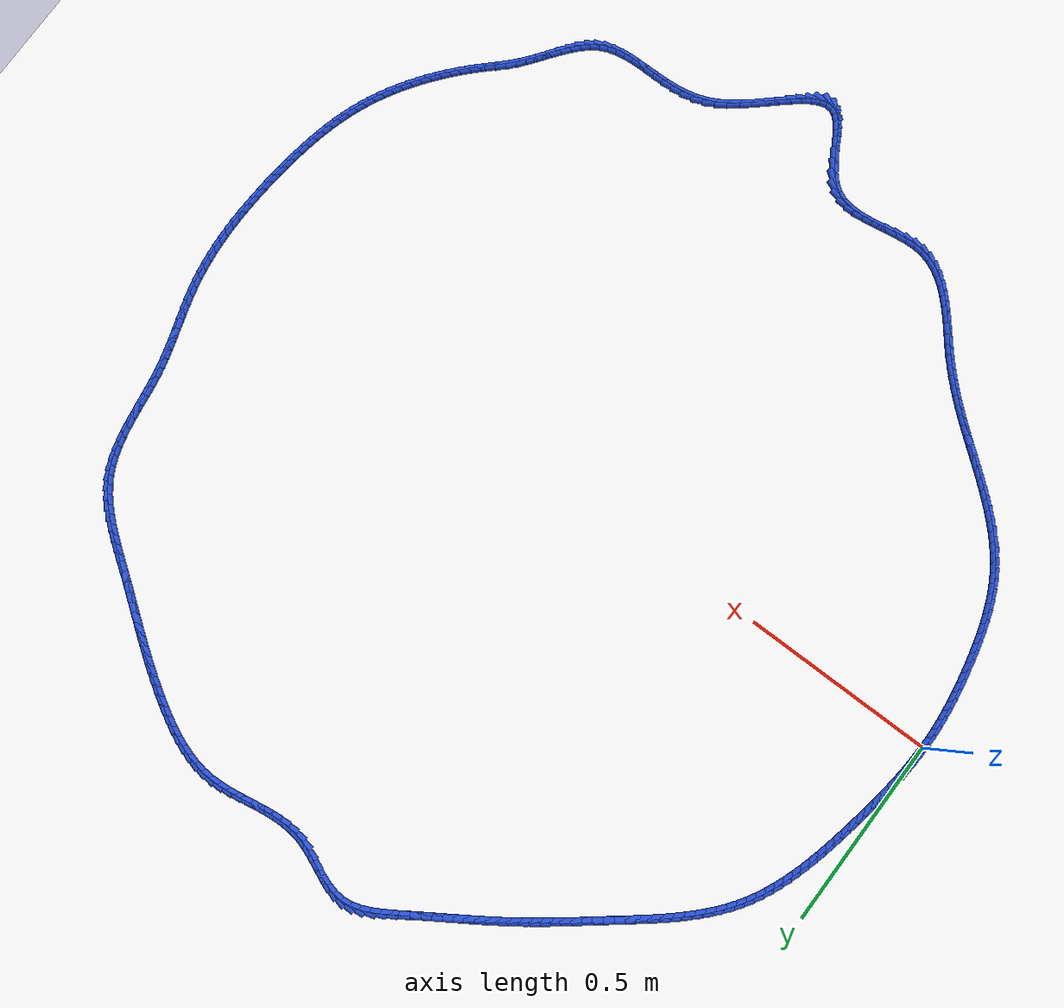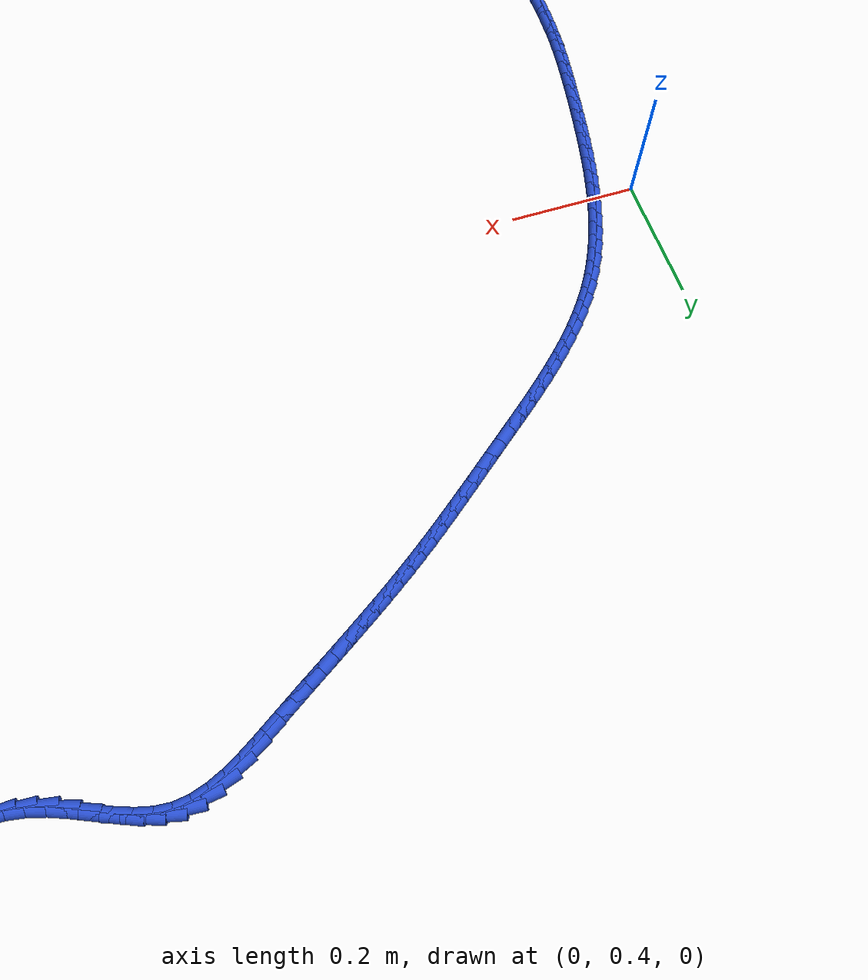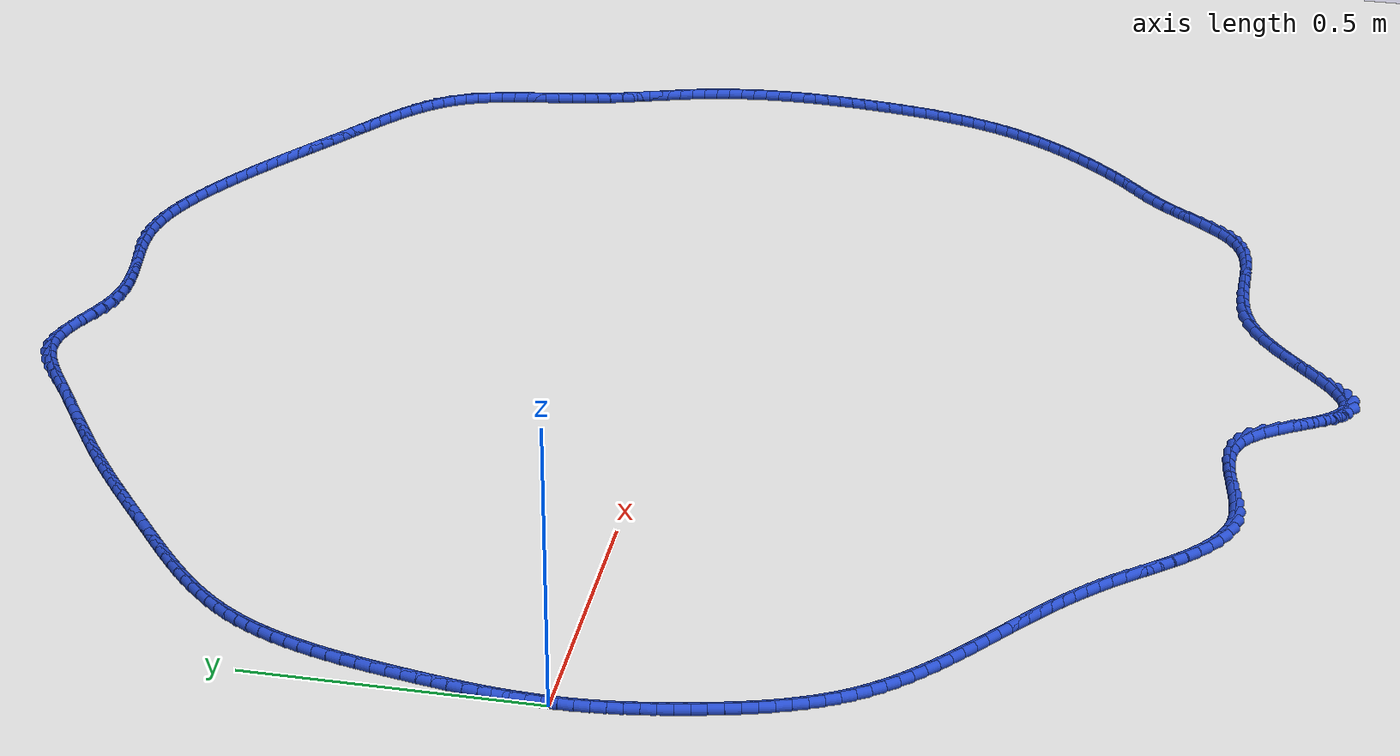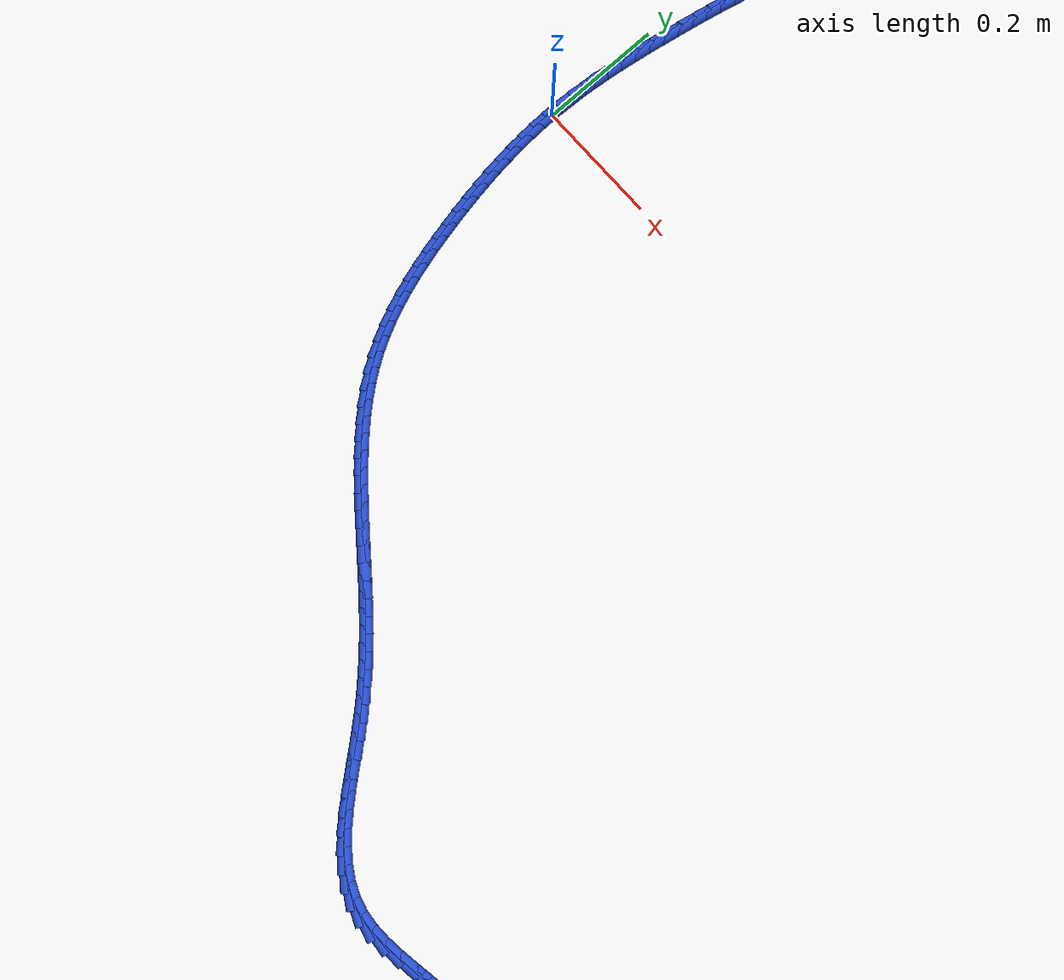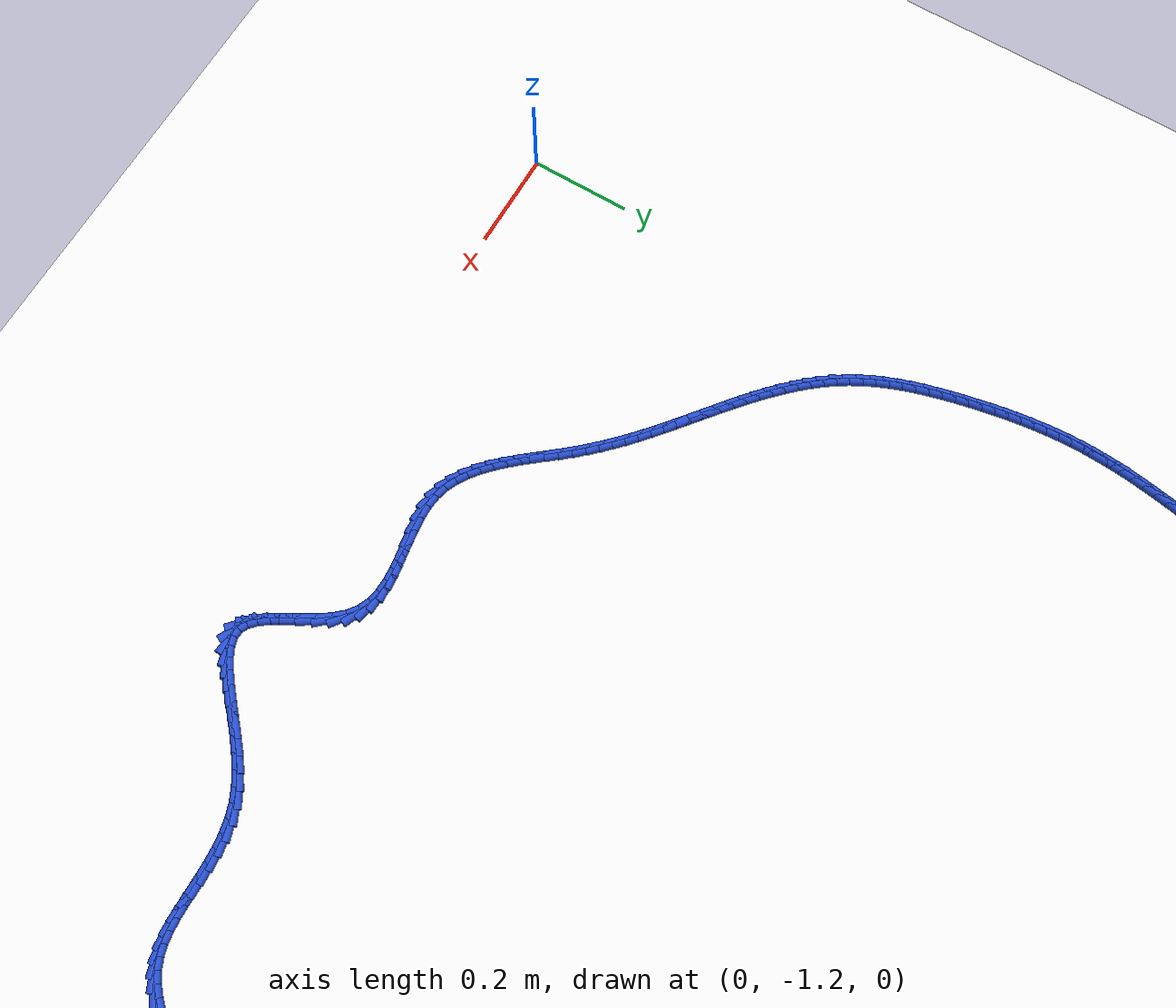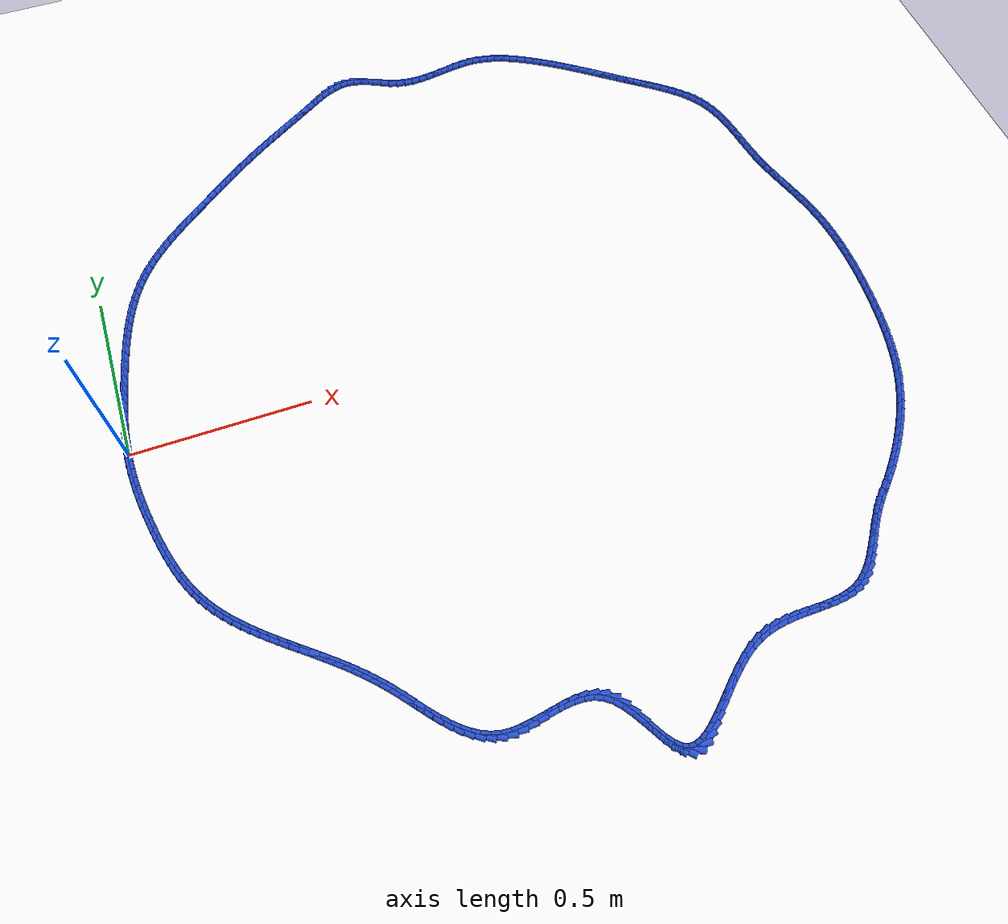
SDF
<sdf version="1.6">
 <world name="default">
  <light name="sun" type="directional">
   <pose>0 0 10 0 -0 0</pose>
   <diffuse>0.8 0.8 0.8 1</diffuse>
   <specular>0.2 0.2 0.2 1</specular>
   <attenuation>
    <range>1000</range>
    <constant>0.9</constant>
    <linear>0.01</linear>
    <quadratic>0.001</quadratic>
   </attenuation>
   <direction>-0.5 0.1 -0.9</direction>
  </light>
  <model name="ground_plane">
   <static>1</static>
   <link name="link">
    <collision name="collision">
     <geometry><plane><normal>0 0 1</normal><size>100 100</size></plane></geometry>
     <surface><friction><ode><mu>100</mu><mu2>50</mu2></ode></friction></surface>
    </collision>
    <visual name="visual">
     <cast_shadows>0</cast_shadows>
     <geometry><plane><normal>0 0 1</normal><size>100 100</size></plane></geometry>
     <material>
      <script><uri>file://media/materials/scripts/gazebo.material</uri><name>Gazebo/WhiteGlow</name></script>
     </material>
    </visual>
   </link>
  </model>
  <gravity>0 0 -9.8</gravity>
  <magnetic_field>6e-06 2.3e-05 -4.2e-05</magnetic_field>
  <atmosphere type="adiabatic"/>
  <physics name="default_physics" default="0" type="ode">
   <max_step_size>0.001</max_step_size>
   <real_time_factor>1</real_time_factor>
   <real_time_update_rate>1000</real_time_update_rate>
  </physics>
  <scene><ambient>0.4 0.4 0.4 1</ambient><background>0.7 0.7 0.7 1</background><shadows>1</shadows></scene>
  <spherical_coordinates>
   <surface_model>EARTH_WGS84</surface_model>
   <latitude_deg>0</latitude_deg>
   <longitude_deg>0</longitude_deg>
   <elevation>0</elevation>
   <heading_deg>0</heading_deg>
  </spherical_coordinates>
  <model name="line">
   <link name="link_0">
    <pose>-3.122502256758253e-17 4.163336342344337e-17 0.01 0 1.57 1.5473795753118187</pose>
    <collision name="collision">
     <geometry><cylinder><radius>0.01</radius><length>0.08</length></cylinder></geometry>
    </collision>
    <visual name="visual">
     <material>
      <script><name>Gazebo/Blue</name><uri>file://media/materials/scripts/gazebo.material</uri></script>
     </material>
     <geometry><cylinder><radius>0.01</radius><length>0.08</length></cylinder></geometry>
    </visual>
   </link>
   <link name="link_1">
    <pose>0.0005900893197626238 0.02519484647066021 0.01 0 1.57 1.5175315877258198</pose>
    <collision name="collision">
     <geometry><cylinder><radius>0.01</radius><length>0.08</length></cylinder></geometry>
    </collision>
    <visual name="visual">
     <material>
      <script><name>Gazebo/Blue</name><uri>file://media/materials/scripts/gazebo.material</uri></script>
     </material>
     <geometry><cylinder><radius>0.01</radius><length>0.08</length></cylinder></geometry>
    </visual>
   </link>
   <link name="link_2">
    <pose>0.0019326716595127892 0.05037684169571538 0.01 0 1.57 1.4906337759523802</pose>
    <collision name="collision">
     <geometry><cylinder><radius>0.01</radius><length>0.08</length></cylinder></geometry>
    </collision>
    <visual name="visual">
     <material>
      <script><name>Gazebo/Blue</name><uri>file://media/materials/scripts/gazebo.material</uri></script>
     </material>
     <geometry><cylinder><radius>0.01</radius><length>0.08</length></cylinder></geometry>
    </visual>
   </link>
   <link name="link_3">
    <pose>0.003955560160450149 0.07555759719595234 0.01 0 1.57 1.4667317699135582</pose>
    <collision name="collision">
     <geometry><cylinder><radius>0.01</radius><length>0.08</length></cylinder></geometry>
    </collision>
    <visual name="visual">
     <material>
      <script><name>Gazebo/Blue</name><uri>file://media/materials/scripts/gazebo.material</uri></script>
     </material>
     <geometry><cylinder><radius>0.01</radius><length>0.08</length></cylinder></geometry>
    </visual>
   </link>
   <link name="link_4">
    <pose>0.006586567963774382 0.10074872449215784 0.01 0 1.57 1.4458438301383736</pose>
    <collision name="collision">
     <geometry><cylinder><radius>0.01</radius><length>0.08</length></cylinder></geometry>
    </collision>
    <visual name="visual">
     <material>
      <script><name>Gazebo/Blue</name><uri>file://media/materials/scripts/gazebo.material</uri></script>
     </material>
     <geometry><cylinder><radius>0.01</radius><length>0.08</length></cylinder></geometry>
    </visual>
   </link>
   <link name="link_5">
    <pose>0.009753508210685173 0.12596183510511866 0.01 0 1.57 1.4279672610065628</pose>
    <collision name="collision">
     <geometry><cylinder><radius>0.01</radius><length>0.08</length></cylinder></geometry>
    </collision>
    <visual name="visual">
     <material>
      <script><name>Gazebo/Blue</name><uri>file://media/materials/scripts/gazebo.material</uri></script>
     </material>
     <geometry><cylinder><radius>0.01</radius><length>0.08</length></cylinder></geometry>
    </visual>
   </link>
   <link name="link_6">
    <pose>0.013384194042382214 0.1512085405556217 0.01 0 1.57 1.413084225599685</pose>
    <collision name="collision">
     <geometry><cylinder><radius>0.01</radius><length>0.08</length></cylinder></geometry>
    </collision>
    <visual name="visual">
     <material>
      <script><name>Gazebo/Blue</name><uri>file://media/materials/scripts/gazebo.material</uri></script>
     </material>
     <geometry><cylinder><radius>0.01</radius><length>0.08</length></cylinder></geometry>
    </visual>
   </link>
   <link name="link_7">
    <pose>0.017406438600065174 0.1765004523644535 0.01 0 1.57 1.4011667552382052</pose>
    <collision name="collision">
     <geometry><cylinder><radius>0.01</radius><length>0.08</length></cylinder></geometry>
    </collision>
    <visual name="visual">
     <material>
      <script><name>Gazebo/Blue</name><uri>file://media/materials/scripts/gazebo.material</uri></script>
     </material>
     <geometry><cylinder><radius>0.01</radius><length>0.08</length></cylinder></geometry>
    </visual>
   </link>
   <link name="link_8">
    <pose>0.021748055024933738 0.20184918205240104 0.01 0 1.57 1.3921808598402106</pose>
    <collision name="collision">
     <geometry><cylinder><radius>0.01</radius><length>0.08</length></cylinder></geometry>
    </collision>
    <visual name="visual">
     <material>
      <script><name>Gazebo/Blue</name><uri>file://media/materials/scripts/gazebo.material</uri></script>
     </material>
     <geometry><cylinder><radius>0.01</radius><length>0.08</length></cylinder></geometry>
    </visual>
   </link>
   <link name="link_9">
    <pose>0.026336856458187598 0.22726634114025107 0.01 0 1.57 1.3854232616919095</pose>
    <collision name="collision">
     <geometry><cylinder><radius>0.01</radius><length>0.08</length></cylinder></geometry>
    </collision>
    <visual name="visual">
     <material>
      <script><name>Gazebo/Blue</name><uri>file://media/materials/scripts/gazebo.material</uri></script>
     </material>
     <geometry><cylinder><radius>0.01</radius><length>0.08</length></cylinder></geometry>
    </visual>
   </link>
   <link name="link_10">
    <pose>0.031116711293106804 0.25275536602874654 0.01 0 1.57 1.3768954850194726</pose>
    <collision name="collision">
     <geometry><cylinder><radius>0.01</radius><length>0.08</length></cylinder></geometry>
    </collision>
    <visual name="visual">
     <material>
      <script><name>Gazebo/Blue</name><uri>file://media/materials/scripts/gazebo.material</uri></script>
     </material>
     <geometry><cylinder><radius>0.01</radius><length>0.08</length></cylinder></geometry>
    </visual>
   </link>
   <link name="link_11">
    <pose>0.036127161319846245 0.27827097750205015 0.01 0 1.57 1.3651088504605655</pose>
    <collision name="collision">
     <geometry><cylinder><radius>0.01</radius><length>0.08</length></cylinder></geometry>
    </collision>
    <visual name="visual">
     <material>
      <script><name>Gazebo/Blue</name><uri>file://media/materials/scripts/gazebo.material</uri></script>
     </material>
     <geometry><cylinder><radius>0.01</radius><length>0.08</length></cylinder></geometry>
    </visual>
   </link>
   <link name="link_12">
    <pose>0.041443041089108304 0.3037499257417638 0.01 0 1.57 1.350009877731286</pose>
    <collision name="collision">
     <geometry><cylinder><radius>0.01</radius><length>0.08</length></cylinder></geometry>
    </collision>
    <visual name="visual">
     <material>
      <script><name>Gazebo/Blue</name><uri>file://media/materials/scripts/gazebo.material</uri></script>
     </material>
     <geometry><cylinder><radius>0.01</radius><length>0.08</length></cylinder></geometry>
    </visual>
   </link>
   <link name="link_13">
    <pose>0.04713924096553251 0.3291289325097771 0.01 0 1.57 1.3315191220687965</pose>
    <collision name="collision">
     <geometry><cylinder><radius>0.01</radius><length>0.08</length></cylinder></geometry>
    </collision>
    <visual name="visual">
     <material>
      <script><name>Gazebo/Blue</name><uri>file://media/materials/scripts/gazebo.material</uri></script>
     </material>
     <geometry><cylinder><radius>0.01</radius><length>0.08</length></cylinder></geometry>
    </visual>
   </link>
   <link name="link_14">
    <pose>0.053290651313758416 0.35434471956798036 0.01 0 1.57 1.3095327443610911</pose>
    <collision name="collision">
     <geometry><cylinder><radius>0.01</radius><length>0.08</length></cylinder></geometry>
    </collision>
    <visual name="visual">
     <material>
      <script><name>Gazebo/Blue</name><uri>file://media/materials/scripts/gazebo.material</uri></script>
     </material>
     <geometry><cylinder><radius>0.01</radius><length>0.08</length></cylinder></geometry>
    </visual>
   </link>
   <link name="link_15">
    <pose>0.059972162498425546 0.37933400867826333 0.01 0 1.57 1.2839275367372276</pose>
    <collision name="collision">
     <geometry><cylinder><radius>0.01</radius><length>0.08</length></cylinder></geometry>
    </collision>
    <visual name="visual">
     <material>
      <script><name>Gazebo/Blue</name><uri>file://media/materials/scripts/gazebo.material</uri></script>
     </material>
     <geometry><cylinder><radius>0.01</radius><length>0.08</length></cylinder></geometry>
    </visual>
   </link>
   <link name="link_16">
    <pose>0.06725866488417347 0.4040335216025162 0.01 0 1.57 1.2545676279115732</pose>
    <collision name="collision">
     <geometry><cylinder><radius>0.01</radius><length>0.08</length></cylinder></geometry>
    </collision>
    <visual name="visual">
     <material>
      <script><name>Gazebo/Blue</name><uri>file://media/materials/scripts/gazebo.material</uri></script>
     </material>
     <geometry><cylinder><radius>0.01</radius><length>0.08</length></cylinder></geometry>
    </visual>
   </link>
   <link name="link_17">
    <pose>0.07522504883564168 0.4283799801026286 0.01 0 1.57 1.2213134818227265</pose>
    <collision name="collision">
     <geometry><cylinder><radius>0.01</radius><length>0.08</length></cylinder></geometry>
    </collision>
    <visual name="visual">
     <material>
      <script><name>Gazebo/Blue</name><uri>file://media/materials/scripts/gazebo.material</uri></script>
     </material>
     <geometry><cylinder><radius>0.01</radius><length>0.08</length></cylinder></geometry>
    </visual>
   </link>
   <link name="link_18">
    <pose>0.08394620471746972 0.4523101059404908 0.01 0 1.57 1.1840338181467263</pose>
    <collision name="collision">
     <geometry><cylinder><radius>0.01</radius><length>0.08</length></cylinder></geometry>
    </collision>
    <visual name="visual">
     <material>
      <script><name>Gazebo/Blue</name><uri>file://media/materials/scripts/gazebo.material</uri></script>
     </material>
     <geometry><cylinder><radius>0.01</radius><length>0.08</length></cylinder></geometry>
    </visual>
   </link>
   <link name="link_19">
    <pose>0.09349702289429718 0.4757606208779927 0.01 0 1.57 1.1426209841722084</pose>
    <collision name="collision">
     <geometry><cylinder><radius>0.01</radius><length>0.08</length></cylinder></geometry>
    </collision>
    <visual name="visual">
     <material>
      <script><name>Gazebo/Blue</name><uri>file://media/materials/scripts/gazebo.material</uri></script>
     </material>
     <geometry><cylinder><radius>0.01</radius><length>0.08</length></cylinder></geometry>
    </visual>
   </link>
   <link name="link_20">
    <pose>0.10395239373076355 0.49866824667702436 0.01 0 1.57 1.097010016177212</pose>
    <collision name="collision">
     <geometry><cylinder><radius>0.01</radius><length>0.08</length></cylinder></geometry>
    </collision>
    <visual name="visual">
     <material>
      <script><name>Gazebo/Blue</name><uri>file://media/materials/scripts/gazebo.material</uri></script>
     </material>
     <geometry><cylinder><radius>0.01</radius><length>0.08</length></cylinder></geometry>
    </visual>
   </link>
   <link name="link_21">
    <pose>0.11538720759150844 0.5209697050994757 0.01 0 1.57 1.0472010587833755</pose>
    <collision name="collision">
     <geometry><cylinder><radius>0.01</radius><length>0.08</length></cylinder></geometry>
    </collision>
    <visual name="visual">
     <material>
      <script><name>Gazebo/Blue</name><uri>file://media/materials/scripts/gazebo.material</uri></script>
     </material>
     <geometry><cylinder><radius>0.01</radius><length>0.08</length></cylinder></geometry>
    </visual>
   </link>
   <link name="link_22">
    <pose>0.12787635484117127 0.5426017179072364 0.01 0 1.57 0.9934038232384103</pose>
    <collision name="collision">
     <geometry><cylinder><radius>0.01</radius><length>0.08</length></cylinder></geometry>
    </collision>
    <visual name="visual">
     <material>
      <script><name>Gazebo/Blue</name><uri>file://media/materials/scripts/gazebo.material</uri></script>
     </material>
     <geometry><cylinder><radius>0.01</radius><length>0.08</length></cylinder></geometry>
    </visual>
   </link>
   <link name="link_23">
    <pose>0.14149227389564553 0.5635027232913393 0.01 0 1.57 0.9396531943923616</pose>
    <collision name="collision">
     <geometry><cylinder><radius>0.01</radius><length>0.08</length></cylinder></geometry>
    </collision>
    <visual name="visual">
     <material>
      <script><name>Gazebo/Blue</name><uri>file://media/materials/scripts/gazebo.material</uri></script>
     </material>
     <geometry><cylinder><radius>0.01</radius><length>0.08</length></cylinder></geometry>
    </visual>
   </link>
   <link name="link_24">
    <pose>0.1562289866751136 0.5836660530692439 0.01 0 1.57 0.8907208126565039</pose>
    <collision name="collision">
     <geometry><cylinder><radius>0.01</radius><length>0.08</length></cylinder></geometry>
    </collision>
    <visual name="visual">
     <material>
      <script><name>Gazebo/Blue</name><uri>file://media/materials/scripts/gazebo.material</uri></script>
     </material>
     <geometry><cylinder><radius>0.01</radius><length>0.08</length></cylinder></geometry>
    </visual>
   </link>
   <link name="link_25">
    <pose>0.17198747357145278 0.6031501705954753 0.01 0 1.57 0.8469727180315381</pose>
    <collision name="collision">
     <geometry><cylinder><radius>0.01</radius><length>0.08</length></cylinder></geometry>
    </collision>
    <visual name="visual">
     <material>
      <script><name>Gazebo/Blue</name><uri>file://media/materials/scripts/gazebo.material</uri></script>
     </material>
     <geometry><cylinder><radius>0.01</radius><length>0.08</length></cylinder></geometry>
    </visual>
   </link>
   <link name="link_26">
    <pose>0.18866331117971608 0.6220173220256328 0.01 0 1.57 0.8084007828363696</pose>
    <collision name="collision">
     <geometry><cylinder><radius>0.01</radius><length>0.08</length></cylinder></geometry>
    </collision>
    <visual name="visual">
     <material>
      <script><name>Gazebo/Blue</name><uri>file://media/materials/scripts/gazebo.material</uri></script>
     </material>
     <geometry><cylinder><radius>0.01</radius><length>0.08</length></cylinder></geometry>
    </visual>
   </link>
   <link name="link_27">
    <pose>0.20615207609495673 0.6403297535153155 0.01 0 1.57 0.774922695202649</pose>
    <collision name="collision">
     <geometry><cylinder><radius>0.01</radius><length>0.08</length></cylinder></geometry>
    </collision>
    <visual name="visual">
     <material>
      <script><name>Gazebo/Blue</name><uri>file://media/materials/scripts/gazebo.material</uri></script>
     </material>
     <geometry><cylinder><radius>0.01</radius><length>0.08</length></cylinder></geometry>
    </visual>
   </link>
   <link name="link_28">
    <pose>0.2243493449122274 0.6581497112201221 0.01 0 1.57 0.746413307049353</pose>
    <collision name="collision">
     <geometry><cylinder><radius>0.01</radius><length>0.08</length></cylinder></geometry>
    </collision>
    <visual name="visual">
     <material>
      <script><name>Gazebo/Blue</name><uri>file://media/materials/scripts/gazebo.material</uri></script>
     </material>
     <geometry><cylinder><radius>0.01</radius><length>0.08</length></cylinder></geometry>
    </visual>
   </link>
   <link name="link_29">
    <pose>0.24315069422658128 0.6755394412956518 0.01 0 1.57 0.7227301949084424</pose>
    <collision name="collision">
     <geometry><cylinder><radius>0.01</radius><length>0.08</length></cylinder></geometry>
    </collision>
    <visual name="visual">
     <material>
      <script><name>Gazebo/Blue</name><uri>file://media/materials/scripts/gazebo.material</uri></script>
     </material>
     <geometry><cylinder><radius>0.01</radius><length>0.08</length></cylinder></geometry>
    </visual>
   </link>
   <link name="link_30">
    <pose>0.26245170063307144 0.6925611898975038 0.01 0 1.57 0.7037333828109048</pose>
    <collision name="collision">
     <geometry><cylinder><radius>0.01</radius><length>0.08</length></cylinder></geometry>
    </collision>
    <visual name="visual">
     <material>
      <script><name>Gazebo/Blue</name><uri>file://media/materials/scripts/gazebo.material</uri></script>
     </material>
     <geometry><cylinder><radius>0.01</radius><length>0.08</length></cylinder></geometry>
    </visual>
   </link>
   <link name="link_31">
    <pose>0.28214794072675065 0.7092772031812767 0.01 0 1.57 0.6892999257215536</pose>
    <collision name="collision">
     <geometry><cylinder><radius>0.01</radius><length>0.08</length></cylinder></geometry>
    </collision>
    <visual name="visual">
     <material>
      <script><name>Gazebo/Blue</name><uri>file://media/materials/scripts/gazebo.material</uri></script>
     </material>
     <geometry><cylinder><radius>0.01</radius><length>0.08</length></cylinder></geometry>
    </visual>
   </link>
   <link name="link_32">
    <pose>0.3021349911026723 0.7257497273025703 0.01 0 1.57 0.6793343324621144</pose>
    <collision name="collision">
     <geometry><cylinder><radius>0.01</radius><length>0.08</length></cylinder></geometry>
    </collision>
    <visual name="visual">
     <material>
      <script><name>Gazebo/Blue</name><uri>file://media/materials/scripts/gazebo.material</uri></script>
     </material>
     <geometry><cylinder><radius>0.01</radius><length>0.08</length></cylinder></geometry>
    </visual>
   </link>
   <link name="link_33">
    <pose>0.322308428355889 0.7420410084169826 0.01 0 1.57 0.6737757963437292</pose>
    <collision name="collision">
     <geometry><cylinder><radius>0.01</radius><length>0.08</length></cylinder></geometry>
    </collision>
    <visual name="visual">
     <material>
      <script><name>Gazebo/Blue</name><uri>file://media/materials/scripts/gazebo.material</uri></script>
     </material>
     <geometry><cylinder><radius>0.01</radius><length>0.08</length></cylinder></geometry>
    </visual>
   </link>
   <link name="link_34">
    <pose>0.34256382908145405 0.7582132926801137 0.01 0 1.57 0.672583016137868</pose>
    <collision name="collision">
     <geometry><cylinder><radius>0.01</radius><length>0.08</length></cylinder></geometry>
    </collision>
    <visual name="visual">
     <material>
      <script><name>Gazebo/Blue</name><uri>file://media/materials/scripts/gazebo.material</uri></script>
     </material>
     <geometry><cylinder><radius>0.01</radius><length>0.08</length></cylinder></geometry>
    </visual>
   </link>
   <link name="link_35">
    <pose>0.3627971862684209 0.7743284958955404 0.01 0 1.57 0.6737347139427622</pose>
    <collision name="collision">
     <geometry><cylinder><radius>0.01</radius><length>0.08</length></cylinder></geometry>
    </collision>
    <visual name="visual">
     <material>
      <script><name>Gazebo/Blue</name><uri>file://media/materials/scripts/gazebo.material</uri></script>
     </material>
     <geometry><cylinder><radius>0.01</radius><length>0.08</length></cylinder></geometry>
    </visual>
   </link>
   <link name="link_36">
    <pose>0.38294680408860193 0.7904149656964928 0.01 0 1.57 0.6734707279106257</pose>
    <collision name="collision">
     <geometry><cylinder><radius>0.01</radius><length>0.08</length></cylinder></geometry>
    </collision>
    <visual name="visual">
     <material>
      <script><name>Gazebo/Blue</name><uri>file://media/materials/scripts/gazebo.material</uri></script>
     </material>
     <geometry><cylinder><radius>0.01</radius><length>0.08</length></cylinder></geometry>
    </visual>
   </link>
   <link name="link_37">
    <pose>0.4030291421284044 0.806439044021731 0.01 0 1.57 0.6713654756858886</pose>
    <collision name="collision">
     <geometry><cylinder><radius>0.01</radius><length>0.08</length></cylinder></geometry>
    </collision>
    <visual name="visual">
     <material>
      <script><name>Gazebo/Blue</name><uri>file://media/materials/scripts/gazebo.material</uri></script>
     </material>
     <geometry><cylinder><radius>0.01</radius><length>0.08</length></cylinder></geometry>
    </visual>
   </link>
   <link name="link_38">
    <pose>0.42306910291835326 0.8223603744818692 0.01 0 1.57 0.6673965449942747</pose>
    <collision name="collision">
     <geometry><cylinder><radius>0.01</radius><length>0.08</length></cylinder></geometry>
    </collision>
    <visual name="visual">
     <material>
      <script><name>Gazebo/Blue</name><uri>file://media/materials/scripts/gazebo.material</uri></script>
     </material>
     <geometry><cylinder><radius>0.01</radius><length>0.08</length></cylinder></geometry>
    </visual>
   </link>
   <link name="link_39">
    <pose>0.44309158898897316 0.838138600687521 0.01 0 1.57 0.6615389418892058</pose>
    <collision name="collision">
     <geometry><cylinder><radius>0.01</radius><length>0.08</length></cylinder></geometry>
    </collision>
    <visual name="visual">
     <material>
      <script><name>Gazebo/Blue</name><uri>file://media/materials/scripts/gazebo.material</uri></script>
     </material>
     <geometry><cylinder><radius>0.01</radius><length>0.08</length></cylinder></geometry>
    </visual>
   </link>
   <link name="link_40">
    <pose>0.4631215028707886 0.8537333662493005 0.01 0 1.57 0.653765410674044</pose>
    <collision name="collision">
     <geometry><cylinder><radius>0.01</radius><length>0.08</length></cylinder></geometry>
    </collision>
    <visual name="visual">
     <material>
      <script><name>Gazebo/Blue</name><uri>file://media/materials/scripts/gazebo.material</uri></script>
     </material>
     <geometry><cylinder><radius>0.01</radius><length>0.08</length></cylinder></geometry>
    </visual>
   </link>
   <link name="link_41">
    <pose>0.483183747094325 0.869104314777822 0.01 0 1.57 0.6440469759912804</pose>
    <collision name="collision">
     <geometry><cylinder><radius>0.01</radius><length>0.08</length></cylinder></geometry>
    </collision>
    <visual name="visual">
     <material>
      <script><name>Gazebo/Blue</name><uri>file://media/materials/scripts/gazebo.material</uri></script>
     </material>
     <geometry><cylinder><radius>0.01</radius><length>0.08</length></cylinder></geometry>
    </visual>
   </link>
   <link name="link_42">
    <pose>0.5033032241901063 0.8842110898836989 0.01 0 1.57 0.6323537324862533</pose>
    <collision name="collision">
     <geometry><cylinder><radius>0.01</radius><length>0.08</length></cylinder></geometry>
    </collision>
    <visual name="visual">
     <material>
      <script><name>Gazebo/Blue</name><uri>file://media/materials/scripts/gazebo.material</uri></script>
     </material>
     <geometry><cylinder><radius>0.01</radius><length>0.08</length></cylinder></geometry>
    </visual>
   </link>
   <link name="link_43">
    <pose>0.5235048366886577 0.8990133351775456 0.01 0 1.57 0.6189586472472137</pose>
    <collision name="collision">
     <geometry><cylinder><radius>0.01</radius><length>0.08</length></cylinder></geometry>
    </collision>
    <visual name="visual">
     <material>
      <script><name>Gazebo/Blue</name><uri>file://media/materials/scripts/gazebo.material</uri></script>
     </material>
     <geometry><cylinder><radius>0.01</radius><length>0.08</length></cylinder></geometry>
    </visual>
   </link>
   <link name="link_44">
    <pose>0.5438129419304345 0.9134795718546239 0.01 0 1.57 0.6062135328782154</pose>
    <collision name="collision">
     <geometry><cylinder><radius>0.01</radius><length>0.08</length></cylinder></geometry>
    </collision>
    <visual name="visual">
     <material>
      <script><name>Gazebo/Blue</name><uri>file://media/materials/scripts/gazebo.material</uri></script>
     </material>
     <geometry><cylinder><radius>0.01</radius><length>0.08</length></cylinder></geometry>
    </visual>
   </link>
   <link name="link_45">
    <pose>0.5642476838814152 0.9276469294555973 0.01 0 1.57 0.5952959513549528</pose>
    <collision name="collision">
     <geometry><cylinder><radius>0.01</radius><length>0.08</length></cylinder></geometry>
    </collision>
    <visual name="visual">
     <material>
      <script><name>Gazebo/Blue</name><uri>file://media/materials/scripts/gazebo.material</uri></script>
     </material>
     <geometry><cylinder><radius>0.01</radius><length>0.08</length></cylinder></geometry>
    </visual>
   </link>
   <link name="link_46">
    <pose>0.5848272435452601 0.9415845013537882 0.01 0 1.57 0.5862882250345604</pose>
    <collision name="collision">
     <geometry><cylinder><radius>0.01</radius><length>0.08</length></cylinder></geometry>
    </collision>
    <visual name="visual">
     <material>
      <script><name>Gazebo/Blue</name><uri>file://media/materials/scripts/gazebo.material</uri></script>
     </material>
     <geometry><cylinder><radius>0.01</radius><length>0.08</length></cylinder></geometry>
    </visual>
   </link>
   <link name="link_47">
    <pose>0.6055697909525449 0.9553615596023771 0.01 0 1.57 0.5792393897039184</pose>
    <collision name="collision">
     <geometry><cylinder><radius>0.01</radius><length>0.08</length></cylinder></geometry>
    </collision>
    <visual name="visual">
     <material>
      <script><name>Gazebo/Blue</name><uri>file://media/materials/scripts/gazebo.material</uri></script>
     </material>
     <geometry><cylinder><radius>0.01</radius><length>0.08</length></cylinder></geometry>
    </visual>
   </link>
   <link name="link_48">
    <pose>0.626493496133846 0.9690473762545446 0.01 0 1.57 0.5741714128026425</pose>
    <collision name="collision">
     <geometry><cylinder><radius>0.01</radius><length>0.08</length></cylinder></geometry>
    </collision>
    <visual name="visual">
     <material>
      <script><name>Gazebo/Blue</name><uri>file://media/materials/scripts/gazebo.material</uri></script>
     </material>
     <geometry><cylinder><radius>0.01</radius><length>0.08</length></cylinder></geometry>
    </visual>
   </link>
   <link name="link_49">
    <pose>0.6476165291197394 0.9827112233634712 0.01 0 1.57 0.5710800401883386</pose>
    <collision name="collision">
     <geometry><cylinder><radius>0.01</radius><length>0.08</length></cylinder></geometry>
    </collision>
    <visual name="visual">
     <material>
      <script><name>Gazebo/Blue</name><uri>file://media/materials/scripts/gazebo.material</uri></script>
     </material>
     <geometry><cylinder><radius>0.01</radius><length>0.08</length></cylinder></geometry>
    </visual>
   </link>
   <link name="link_50">
    <pose>0.668957059940801 0.9964223729823366 0.01 0 1.57 0.5699362455939248</pose>
    <collision name="collision">
     <geometry><cylinder><radius>0.01</radius><length>0.08</length></cylinder></geometry>
    </collision>
    <visual name="visual">
     <material>
      <script><name>Gazebo/Blue</name><uri>file://media/materials/scripts/gazebo.material</uri></script>
     </material>
     <geometry><cylinder><radius>0.01</radius><length>0.08</length></cylinder></geometry>
    </visual>
   </link>
   <link name="link_51">
    <pose>0.6905332586276066 1.0102500971643218 0.01 0 1.57 0.5706881623914819</pose>
    <collision name="collision">
     <geometry><cylinder><radius>0.01</radius><length>0.08</length></cylinder></geometry>
    </collision>
    <visual name="visual">
     <material>
      <script><name>Gazebo/Blue</name><uri>file://media/materials/scripts/gazebo.material</uri></script>
     </material>
     <geometry><cylinder><radius>0.01</radius><length>0.08</length></cylinder></geometry>
    </visual>
   </link>
   <link name="link_52">
    <pose>0.7123632952107328 1.0242636679626074 0.01 0 1.57 0.5732633837373443</pose>
    <collision name="collision">
     <geometry><cylinder><radius>0.01</radius><length>0.08</length></cylinder></geometry>
    </collision>
    <visual name="visual">
     <material>
      <script><name>Gazebo/Blue</name><uri>file://media/materials/scripts/gazebo.material</uri></script>
     </material>
     <geometry><cylinder><radius>0.01</radius><length>0.08</length></cylinder></geometry>
    </visual>
   </link>
   <link name="link_53">
    <pose>0.7344653397207553 1.0385323574303733 0.01 0 1.57 0.5775712684854327</pose>
    <collision name="collision">
     <geometry><cylinder><radius>0.01</radius><length>0.08</length></cylinder></geometry>
    </collision>
    <visual name="visual">
     <material>
      <script><name>Gazebo/Blue</name><uri>file://media/materials/scripts/gazebo.material</uri></script>
     </material>
     <geometry><cylinder><radius>0.01</radius><length>0.08</length></cylinder></geometry>
    </visual>
   </link>
   <link name="link_54">
    <pose>0.7568575617105875 1.053125429020058 0.01 0 1.57 0.5780664597320873</pose>
    <collision name="collision">
     <geometry><cylinder><radius>0.01</radius><length>0.08</length></cylinder></geometry>
    </collision>
    <visual name="visual">
     <material>
      <script><name>Gazebo/Blue</name><uri>file://media/materials/scripts/gazebo.material</uri></script>
     </material>
     <geometry><cylinder><radius>0.01</radius><length>0.08</length></cylinder></geometry>
    </visual>
   </link>
   <link name="link_55">
    <pose>0.7795479498108024 1.0679288296686655 0.01 0 1.57 0.5552745668162153</pose>
    <collision name="collision">
     <geometry><cylinder><radius>0.01</radius><length>0.08</length></cylinder></geometry>
    </collision>
    <visual name="visual">
     <material>
      <script><name>Gazebo/Blue</name><uri>file://media/materials/scripts/gazebo.material</uri></script>
     </material>
     <geometry><cylinder><radius>0.01</radius><length>0.08</length></cylinder></geometry>
    </visual>
   </link>
   <link name="link_56">
    <pose>0.8025080863741231 1.0821729790659695 0.01 0 1.57 0.5032574268421592</pose>
    <collision name="collision">
     <geometry><cylinder><radius>0.01</radius><length>0.08</length></cylinder></geometry>
    </collision>
    <visual name="visual">
     <material>
      <script><name>Gazebo/Blue</name><uri>file://media/materials/scripts/gazebo.material</uri></script>
     </material>
     <geometry><cylinder><radius>0.01</radius><length>0.08</length></cylinder></geometry>
    </visual>
   </link>
   <link name="link_57">
    <pose>0.8257014192618498 1.0949418281858048 0.01 0 1.57 0.41757989636411624</pose>
    <collision name="collision">
     <geometry><cylinder><radius>0.01</radius><length>0.08</length></cylinder></geometry>
    </collision>
    <visual name="visual">
     <material>
      <script><name>Gazebo/Blue</name><uri>file://media/materials/scripts/gazebo.material</uri></script>
     </material>
     <geometry><cylinder><radius>0.01</radius><length>0.08</length></cylinder></geometry>
    </visual>
   </link>
   <link name="link_58">
    <pose>0.8490913963352844 1.105319328002008 0.01 0 1.57 0.2916547116022732</pose>
    <collision name="collision">
     <geometry><cylinder><radius>0.01</radius><length>0.08</length></cylinder></geometry>
    </collision>
    <visual name="visual">
     <material>
      <script><name>Gazebo/Blue</name><uri>file://media/materials/scripts/gazebo.material</uri></script>
     </material>
     <geometry><cylinder><radius>0.01</radius><length>0.08</length></cylinder></geometry>
    </visual>
   </link>
   <link name="link_59">
    <pose>0.8726414654557277 1.1123894294884138 0.01 0 1.57 0.11967131604866799</pose>
    <collision name="collision">
     <geometry><cylinder><radius>0.01</radius><length>0.08</length></cylinder></geometry>
    </collision>
    <visual name="visual">
     <material>
      <script><name>Gazebo/Blue</name><uri>file://media/materials/scripts/gazebo.material</uri></script>
     </material>
     <geometry><cylinder><radius>0.01</radius><length>0.08</length></cylinder></geometry>
    </visual>
   </link>
   <link name="link_60">
    <pose>0.896315074484481 1.1152360836188584 0.01 0 1.57 -0.08290072320201426</pose>
    <collision name="collision">
     <geometry><cylinder><radius>0.01</radius><length>0.08</length></cylinder></geometry>
    </collision>
    <visual name="visual">
     <material>
      <script><name>Gazebo/Blue</name><uri>file://media/materials/scripts/gazebo.material</uri></script>
     </material>
     <geometry><cylinder><radius>0.01</radius><length>0.08</length></cylinder></geometry>
    </visual>
   </link>
   <link name="link_61">
    <pose>0.9200845213574799 1.1132610527223379 0.01 0 1.57 -0.2445703732241813</pose>
    <collision name="collision">
     <geometry><cylinder><radius>0.01</radius><length>0.08</length></cylinder></geometry>
    </collision>
    <visual name="visual">
     <material>
      <script><name>Gazebo/Blue</name><uri>file://media/materials/scripts/gazebo.material</uri></script>
     </material>
     <geometry><cylinder><radius>0.01</radius><length>0.08</length></cylinder></geometry>
    </visual>
   </link>
   <link name="link_62">
    <pose>0.9439620899557323 1.107302017796957 0.01 0 1.57 -0.347643867896469</pose>
    <collision name="collision">
     <geometry><cylinder><radius>0.01</radius><length>0.08</length></cylinder></geometry>
    </collision>
    <visual name="visual">
     <material>
      <script><name>Gazebo/Blue</name><uri>file://media/materials/scripts/gazebo.material</uri></script>
     </material>
     <geometry><cylinder><radius>0.01</radius><length>0.08</length></cylinder></geometry>
    </visual>
   </link>
   <link name="link_63">
    <pose>0.967971351775277 1.0986020046969172 0.01 0 1.57 -0.39934482599667137</pose>
    <collision name="collision">
     <geometry><cylinder><radius>0.01</radius><length>0.08</length></cylinder></geometry>
    </collision>
    <visual name="visual">
     <material>
      <script><name>Gazebo/Blue</name><uri>file://media/materials/scripts/gazebo.material</uri></script>
     </material>
     <geometry><cylinder><radius>0.01</radius><length>0.08</length></cylinder></geometry>
    </visual>
   </link>
   <link name="link_64">
    <pose>0.9921358789809869 1.0884040632946708 0.01 0 1.57 -0.4055839112769478</pose>
    <collision name="collision">
     <geometry><cylinder><radius>0.01</radius><length>0.08</length></cylinder></geometry>
    </collision>
    <visual name="visual">
     <material>
      <script><name>Gazebo/Blue</name><uri>file://media/materials/scripts/gazebo.material</uri></script>
     </material>
     <geometry><cylinder><radius>0.01</radius><length>0.08</length></cylinder></geometry>
    </visual>
   </link>
   <link name="link_65">
    <pose>1.0164792437377346 1.0779512434626701 0.01 0 1.57 -0.3680241096204158</pose>
    <collision name="collision">
     <geometry><cylinder><radius>0.01</radius><length>0.08</length></cylinder></geometry>
    </collision>
    <visual name="visual">
     <material>
      <script><name>Gazebo/Blue</name><uri>file://media/materials/scripts/gazebo.material</uri></script>
     </material>
     <geometry><cylinder><radius>0.01</radius><length>0.08</length></cylinder></geometry>
    </visual>
   </link>
   <link name="link_66">
    <pose>1.041025018210394 1.0684865950733677 0.01 0 1.57 -0.2841068414104589</pose>
    <collision name="collision">
     <geometry><cylinder><radius>0.01</radius><length>0.08</length></cylinder></geometry>
    </collision>
    <visual name="visual">
     <material>
      <script><name>Gazebo/Blue</name><uri>file://media/materials/scripts/gazebo.material</uri></script>
     </material>
     <geometry><cylinder><radius>0.01</radius><length>0.08</length></cylinder></geometry>
    </visual>
   </link>
   <link name="link_67">
    <pose>1.0657967718095103 1.0612530935548805 0.01 0 1.57 -0.163326018810447</pose>
    <collision name="collision">
     <geometry><cylinder><radius>0.01</radius><length>0.08</length></cylinder></geometry>
    </collision>
    <visual name="visual">
     <material>
      <script><name>Gazebo/Blue</name><uri>file://media/materials/scripts/gazebo.material</uri></script>
     </material>
     <geometry><cylinder><radius>0.01</radius><length>0.08</length></cylinder></geometry>
    </visual>
   </link>
   <link name="link_68">
    <pose>1.0908046888551215 1.0571319402369077 0.01 0 1.57 -0.052604988895848644</pose>
    <collision name="collision">
     <geometry><cylinder><radius>0.01</radius><length>0.08</length></cylinder></geometry>
    </collision>
    <visual name="visual">
     <material>
      <script><name>Gazebo/Blue</name><uri>file://media/materials/scripts/gazebo.material</uri></script>
     </material>
     <geometry><cylinder><radius>0.01</radius><length>0.08</length></cylinder></geometry>
    </visual>
   </link>
   <link name="link_69">
    <pose>1.1160145634118857 1.0558045504179205 0.01 0 1.57 0.0354385753306904</pose>
    <collision name="collision">
     <geometry><cylinder><radius>0.01</radius><length>0.08</length></cylinder></geometry>
    </collision>
    <visual name="visual">
     <material>
      <script><name>Gazebo/Blue</name><uri>file://media/materials/scripts/gazebo.material</uri></script>
     </material>
     <geometry><cylinder><radius>0.01</radius><length>0.08</length></cylinder></geometry>
    </visual>
   </link>
   <link name="link_70">
    <pose>1.1413829994484728 1.056703948196631 0.01 0 1.57 0.10009015704699996</pose>
    <collision name="collision">
     <geometry><cylinder><radius>0.01</radius><length>0.08</length></cylinder></geometry>
    </collision>
    <visual name="visual">
     <material>
      <script><name>Gazebo/Blue</name><uri>file://media/materials/scripts/gazebo.material</uri></script>
     </material>
     <geometry><cylinder><radius>0.01</radius><length>0.08</length></cylinder></geometry>
    </visual>
   </link>
   <link name="link_71">
    <pose>1.1668666009335533 1.059263157671752 0.01 0 1.57 0.1419460630791456</pose>
    <collision name="collision">
     <geometry><cylinder><radius>0.01</radius><length>0.08</length></cylinder></geometry>
    </collision>
    <visual name="visual">
     <material>
      <script><name>Gazebo/Blue</name><uri>file://media/materials/scripts/gazebo.material</uri></script>
     </material>
     <geometry><cylinder><radius>0.01</radius><length>0.08</length></cylinder></geometry>
    </visual>
   </link>
   <link name="link_72">
    <pose>1.1924219718357978 1.0629152029419962 0.01 0 1.57 0.16187425932820532</pose>
    <collision name="collision">
     <geometry><cylinder><radius>0.01</radius><length>0.08</length></cylinder></geometry>
    </collision>
    <visual name="visual">
     <material>
      <script><name>Gazebo/Blue</name><uri>file://media/materials/scripts/gazebo.material</uri></script>
     </material>
     <geometry><cylinder><radius>0.01</radius><length>0.08</length></cylinder></geometry>
    </visual>
   </link>
   <link name="link_73">
    <pose>1.2180057161238764 1.0670931081060764 0.01 0 1.57 0.1604010717937389</pose>
    <collision name="collision">
     <geometry><cylinder><radius>0.01</radius><length>0.08</length></cylinder></geometry>
    </collision>
    <visual name="visual">
     <material>
      <script><name>Gazebo/Blue</name><uri>file://media/materials/scripts/gazebo.material</uri></script>
     </material>
     <geometry><cylinder><radius>0.01</radius><length>0.08</length></cylinder></geometry>
    </visual>
   </link>
   <link name="link_74">
    <pose>1.2435744377664593 1.0712298972627052 0.01 0 1.57 0.13745217122147418</pose>
    <collision name="collision">
     <geometry><cylinder><radius>0.01</radius><length>0.08</length></cylinder></geometry>
    </collision>
    <visual name="visual">
     <material>
      <script><name>Gazebo/Blue</name><uri>file://media/materials/scripts/gazebo.material</uri></script>
     </material>
     <geometry><cylinder><radius>0.01</radius><length>0.08</length></cylinder></geometry>
    </visual>
   </link>
   <link name="link_75">
    <pose>1.2690847407322174 1.0747585945105953 0.01 0 1.57 0.09236803059131285</pose>
    <collision name="collision">
     <geometry><cylinder><radius>0.01</radius><length>0.08</length></cylinder></geometry>
    </collision>
    <visual name="visual">
     <material>
      <script><name>Gazebo/Blue</name><uri>file://media/materials/scripts/gazebo.material</uri></script>
     </material>
     <geometry><cylinder><radius>0.01</radius><length>0.08</length></cylinder></geometry>
    </visual>
   </link>
   <link name="link_76">
    <pose>1.2944932289898206 1.0771122239484594 0.01 0 1.57 0.02420375957399733</pose>
    <collision name="collision">
     <geometry><cylinder><radius>0.01</radius><length>0.08</length></cylinder></geometry>
    </collision>
    <visual name="visual">
     <material>
      <script><name>Gazebo/Blue</name><uri>file://media/materials/scripts/gazebo.material</uri></script>
     </material>
     <geometry><cylinder><radius>0.01</radius><length>0.08</length></cylinder></geometry>
    </visual>
   </link>
   <link name="link_77">
    <pose>1.3197565065079386 1.0777238096750101 0.01 0 1.57 -0.06649448323543133</pose>
    <collision name="collision">
     <geometry><cylinder><radius>0.01</radius><length>0.08</length></cylinder></geometry>
    </collision>
    <visual name="visual">
     <material>
      <script><name>Gazebo/Blue</name><uri>file://media/materials/scripts/gazebo.material</uri></script>
     </material>
     <geometry><cylinder><radius>0.01</radius><length>0.08</length></cylinder></geometry>
    </visual>
   </link>
   <link name="link_78">
    <pose>1.3448314190899777 1.076054004571463 0.01 0 1.57 -0.16142711639501295</pose>
    <collision name="collision">
     <geometry><cylinder><radius>0.01</radius><length>0.08</length></cylinder></geometry>
    </collision>
    <visual name="visual">
     <material>
      <script><name>Gazebo/Blue</name><uri>file://media/materials/scripts/gazebo.material</uri></script>
     </material>
     <geometry><cylinder><radius>0.01</radius><length>0.08</length></cylinder></geometry>
    </visual>
   </link>
   <link name="link_79">
    <pose>1.3696787015859937 1.0720077716557193 0.01 0 1.57 -0.24548618376894532</pose>
    <collision name="collision">
     <geometry><cylinder><radius>0.01</radius><length>0.08</length></cylinder></geometry>
    </collision>
    <visual name="visual">
     <material>
      <script><name>Gazebo/Blue</name><uri>file://media/materials/scripts/gazebo.material</uri></script>
     </material>
     <geometry><cylinder><radius>0.01</radius><length>0.08</length></cylinder></geometry>
    </visual>
   </link>
   <link name="link_80">
    <pose>1.3942622273056355 1.0658486321052978 0.01 0 1.57 -0.31817789167550947</pose>
    <collision name="collision">
     <geometry><cylinder><radius>0.01</radius><length>0.08</length></cylinder></geometry>
    </collision>
    <visual name="visual">
     <material>
      <script><name>Gazebo/Blue</name><uri>file://media/materials/scripts/gazebo.material</uri></script>
     </material>
     <geometry><cylinder><radius>0.01</radius><length>0.08</length></cylinder></geometry>
    </visual>
   </link>
   <link name="link_81">
    <pose>1.418545959108762 1.0578503378997623 0.01 0 1.57 -0.37994960598173194</pose>
    <collision name="collision">
     <geometry><cylinder><radius>0.01</radius><length>0.08</length></cylinder></geometry>
    </collision>
    <visual name="visual">
     <material>
      <script><name>Gazebo/Blue</name><uri>file://media/materials/scripts/gazebo.material</uri></script>
     </material>
     <geometry><cylinder><radius>0.01</radius><length>0.08</length></cylinder></geometry>
    </visual>
   </link>
   <link name="link_82">
    <pose>1.442493859855232 1.0482866410186773 0.01 0 1.57 -0.43150180645367564</pose>
    <collision name="collision">
     <geometry><cylinder><radius>0.01</radius><length>0.08</length></cylinder></geometry>
    </collision>
    <visual name="visual">
     <material>
      <script><name>Gazebo/Blue</name><uri>file://media/materials/scripts/gazebo.material</uri></script>
     </material>
     <geometry><cylinder><radius>0.01</radius><length>0.08</length></cylinder></geometry>
    </visual>
   </link>
   <link name="link_83">
    <pose>1.4660698924049045 1.0374312934416057 0.01 0 1.57 -0.4735832094723356</pose>
    <collision name="collision">
     <geometry><cylinder><radius>0.01</radius><length>0.08</length></cylinder></geometry>
    </collision>
    <visual name="visual">
     <material>
      <script><name>Gazebo/Blue</name><uri>file://media/materials/scripts/gazebo.material</uri></script>
     </material>
     <geometry><cylinder><radius>0.01</radius><length>0.08</length></cylinder></geometry>
    </visual>
   </link>
   <link name="link_84">
    <pose>1.4892380196176391 1.0255580471481125 0.01 0 1.57 -0.5068579016628197</pose>
    <collision name="collision">
     <geometry><cylinder><radius>0.01</radius><length>0.08</length></cylinder></geometry>
    </collision>
    <visual name="visual">
     <material>
      <script><name>Gazebo/Blue</name><uri>file://media/materials/scripts/gazebo.material</uri></script>
     </material>
     <geometry><cylinder><radius>0.01</radius><length>0.08</length></cylinder></geometry>
    </visual>
   </link>
   <link name="link_85">
    <pose>1.511962204353295 1.012940654117761 0.01 0 1.57 -0.532018254938925</pose>
    <collision name="collision">
     <geometry><cylinder><radius>0.01</radius><length>0.08</length></cylinder></geometry>
    </collision>
    <visual name="visual">
     <material>
      <script><name>Gazebo/Blue</name><uri>file://media/materials/scripts/gazebo.material</uri></script>
     </material>
     <geometry><cylinder><radius>0.01</radius><length>0.08</length></cylinder></geometry>
    </visual>
   </link>
   <link name="link_86">
    <pose>1.534209465067876 0.9998452191120615 0.01 0 1.57 -0.5525723637971851</pose>
    <collision name="collision">
     <geometry><cylinder><radius>0.01</radius><length>0.08</length></cylinder></geometry>
    </collision>
    <visual name="visual">
     <material>
      <script><name>Gazebo/Blue</name><uri>file://media/materials/scripts/gazebo.material</uri></script>
     </material>
     <geometry><cylinder><radius>0.01</radius><length>0.08</length></cylinder></geometry>
    </visual>
   </link>
   <link name="link_87">
    <pose>1.555998235010774 0.9864091714664015 0.01 0 1.57 -0.571155265082946</pose>
    <collision name="collision">
     <geometry><cylinder><radius>0.01</radius><length>0.08</length></cylinder></geometry>
    </collision>
    <visual name="visual">
     <material>
      <script><name>Gazebo/Blue</name><uri>file://media/materials/scripts/gazebo.material</uri></script>
     </material>
     <geometry><cylinder><radius>0.01</radius><length>0.08</length></cylinder></geometry>
    </visual>
   </link>
   <link name="link_88">
    <pose>1.5773896572800647 0.9726630508912654 0.01 0 1.57 -0.5877139115601648</pose>
    <collision name="collision">
     <geometry><cylinder><radius>0.01</radius><length>0.08</length></cylinder></geometry>
    </collision>
    <visual name="visual">
     <material>
      <script><name>Gazebo/Blue</name><uri>file://media/materials/scripts/gazebo.material</uri></script>
     </material>
     <geometry><cylinder><radius>0.01</radius><length>0.08</length></cylinder></geometry>
    </visual>
   </link>
   <link name="link_89">
    <pose>1.5984461707804634 0.9586341540913725 0.01 0 1.57 -0.6021352877129944</pose>
    <collision name="collision">
     <geometry><cylinder><radius>0.01</radius><length>0.08</length></cylinder></geometry>
    </collision>
    <visual name="visual">
     <material>
      <script><name>Gazebo/Blue</name><uri>file://media/materials/scripts/gazebo.material</uri></script>
     </material>
     <geometry><cylinder><radius>0.01</radius><length>0.08</length></cylinder></geometry>
    </visual>
   </link>
   <link name="link_90">
    <pose>1.6192302144166846 0.9443497777714427 0.01 0 1.57 -0.6143295985337573</pose>
    <collision name="collision">
     <geometry><cylinder><radius>0.01</radius><length>0.08</length></cylinder></geometry>
    </collision>
    <visual name="visual">
     <material>
      <script><name>Gazebo/Blue</name><uri>file://media/materials/scripts/gazebo.material</uri></script>
     </material>
     <geometry><cylinder><radius>0.01</radius><length>0.08</length></cylinder></geometry>
    </visual>
   </link>
   <link name="link_91">
    <pose>1.6398042270934419 0.9298372186361951 0.01 0 1.57 -0.6242300928528152</pose>
    <collision name="collision">
     <geometry><cylinder><radius>0.01</radius><length>0.08</length></cylinder></geometry>
    </collision>
    <visual name="visual">
     <material>
      <script><name>Gazebo/Blue</name><uri>file://media/materials/scripts/gazebo.material</uri></script>
     </material>
     <geometry><cylinder><radius>0.01</radius><length>0.08</length></cylinder></geometry>
    </visual>
   </link>
   <link name="link_92">
    <pose>1.6602306477154514 0.9151237733903489 0.01 0 1.57 -0.6317924586829639</pose>
    <collision name="collision">
     <geometry><cylinder><radius>0.01</radius><length>0.08</length></cylinder></geometry>
    </collision>
    <visual name="visual">
     <material>
      <script><name>Gazebo/Blue</name><uri>file://media/materials/scripts/gazebo.material</uri></script>
     </material>
     <geometry><cylinder><radius>0.01</radius><length>0.08</length></cylinder></geometry>
    </visual>
   </link>
   <link name="link_93">
    <pose>1.6805719151874274 0.9002367387386239 0.01 0 1.57 -0.6369939364894709</pose>
    <collision name="collision">
     <geometry><cylinder><radius>0.01</radius><length>0.08</length></cylinder></geometry>
    </collision>
    <visual name="visual">
     <material>
      <script><name>Gazebo/Blue</name><uri>file://media/materials/scripts/gazebo.material</uri></script>
     </material>
     <geometry><cylinder><radius>0.01</radius><length>0.08</length></cylinder></geometry>
    </visual>
   </link>
   <link name="link_94">
    <pose>1.7008904684140844 0.8852034113857394 0.01 0 1.57 -0.6398322785250471</pose>
    <collision name="collision">
     <geometry><cylinder><radius>0.01</radius><length>0.08</length></cylinder></geometry>
    </collision>
    <visual name="visual">
     <material>
      <script><name>Gazebo/Blue</name><uri>file://media/materials/scripts/gazebo.material</uri></script>
     </material>
     <geometry><cylinder><radius>0.01</radius><length>0.08</length></cylinder></geometry>
    </visual>
   </link>
   <link name="link_95">
    <pose>1.7212487463001371 0.8700510880364147 0.01 0 1.57 -0.6403246547230192</pose>
    <collision name="collision">
     <geometry><cylinder><radius>0.01</radius><length>0.08</length></cylinder></geometry>
    </collision>
    <visual name="visual">
     <material>
      <script><name>Gazebo/Blue</name><uri>file://media/materials/scripts/gazebo.material</uri></script>
     </material>
     <geometry><cylinder><radius>0.01</radius><length>0.08</length></cylinder></geometry>
    </visual>
   </link>
   <link name="link_96">
    <pose>1.7417091877503006 0.8548070653953695 0.01 0 1.57 -0.6385065730186528</pose>
    <collision name="collision">
     <geometry><cylinder><radius>0.01</radius><length>0.08</length></cylinder></geometry>
    </collision>
    <visual name="visual">
     <material>
      <script><name>Gazebo/Blue</name><uri>file://media/materials/scripts/gazebo.material</uri></script>
     </material>
     <geometry><cylinder><radius>0.01</radius><length>0.08</length></cylinder></geometry>
    </visual>
   </link>
   <link name="link_97">
    <pose>1.7623342316692892 0.8394986401673232 0.01 0 1.57 -0.6344308485921261</pose>
    <collision name="collision">
     <geometry><cylinder><radius>0.01</radius><length>0.08</length></cylinder></geometry>
    </collision>
    <visual name="visual">
     <material>
      <script><name>Gazebo/Blue</name><uri>file://media/materials/scripts/gazebo.material</uri></script>
     </material>
     <geometry><cylinder><radius>0.01</radius><length>0.08</length></cylinder></geometry>
    </visual>
   </link>
   <link name="link_98">
    <pose>1.7831863169618176 0.824153109056995 0.01 0 1.57 -0.628608501689054</pose>
    <collision name="collision">
     <geometry><cylinder><radius>0.01</radius><length>0.08</length></cylinder></geometry>
    </collision>
    <visual name="visual">
     <material>
      <script><name>Gazebo/Blue</name><uri>file://media/materials/scripts/gazebo.material</uri></script>
     </material>
     <geometry><cylinder><radius>0.01</radius><length>0.08</length></cylinder></geometry>
    </visual>
   </link>
   <link name="link_99">
    <pose>1.804316000010717 0.8087921325309066 0.01 0 1.57 -0.6275224753653147</pose>
    <collision name="collision">
     <geometry><cylinder><radius>0.01</radius><length>0.08</length></cylinder></geometry>
    </collision>
    <visual name="visual">
     <material>
      <script><name>Gazebo/Blue</name><uri>file://media/materials/scripts/gazebo.material</uri></script>
     </material>
     <geometry><cylinder><radius>0.01</radius><length>0.08</length></cylinder></geometry>
    </visual>
   </link>
   <link name="link_100">
    <pose>1.8255994653065617 0.7933546612125523 0.01 0 1.57 -0.6359704507851976</pose>
    <collision name="collision">
     <geometry><cylinder><radius>0.01</radius><length>0.08</length></cylinder></geometry>
    </collision>
    <visual name="visual">
     <material>
      <script><name>Gazebo/Blue</name><uri>file://media/materials/scripts/gazebo.material</uri></script>
     </material>
     <geometry><cylinder><radius>0.01</radius><length>0.08</length></cylinder></geometry>
    </visual>
   </link>
   <link name="link_101">
    <pose>1.8467803963566243 0.7777167965162552 0.01 0 1.57 -0.6541634719165439</pose>
    <collision name="collision">
     <geometry><cylinder><radius>0.01</radius><length>0.08</length></cylinder></geometry>
    </collision>
    <visual name="visual">
     <material>
      <script><name>Gazebo/Blue</name><uri>file://media/materials/scripts/gazebo.material</uri></script>
     </material>
     <geometry><cylinder><radius>0.01</radius><length>0.08</length></cylinder></geometry>
    </visual>
   </link>
   <link name="link_102">
    <pose>1.8675991667753065 0.7617530698744102 0.01 0 1.57 -0.6824658990812795</pose>
    <collision name="collision">
     <geometry><cylinder><radius>0.01</radius><length>0.08</length></cylinder></geometry>
    </collision>
    <visual name="visual">
     <material>
      <script><name>Gazebo/Blue</name><uri>file://media/materials/scripts/gazebo.material</uri></script>
     </material>
     <geometry><cylinder><radius>0.01</radius><length>0.08</length></cylinder></geometry>
    </visual>
   </link>
   <link name="link_103">
    <pose>1.887796150177008 0.7453380127194101 0.01 0 1.57 -0.7214842749751662</pose>
    <collision name="collision">
     <geometry><cylinder><radius>0.01</radius><length>0.08</length></cylinder></geometry>
    </collision>
    <visual name="visual">
     <material>
      <script><name>Gazebo/Blue</name><uri>file://media/materials/scripts/gazebo.material</uri></script>
     </material>
     <geometry><cylinder><radius>0.01</radius><length>0.08</length></cylinder></geometry>
    </visual>
   </link>
   <link name="link_104">
    <pose>1.9071117201761298 0.7283461564836493 0.01 0 1.57 -0.7720054778882527</pose>
    <collision name="collision">
     <geometry><cylinder><radius>0.01</radius><length>0.08</length></cylinder></geometry>
    </collision>
    <visual name="visual">
     <material>
      <script><name>Gazebo/Blue</name><uri>file://media/materials/scripts/gazebo.material</uri></script>
     </material>
     <geometry><cylinder><radius>0.01</radius><length>0.08</length></cylinder></geometry>
    </visual>
   </link>
   <link name="link_105">
    <pose>1.9252862503870718 0.7106520325995217 0.01 0 1.57 -0.8348820350865378</pose>
    <collision name="collision">
     <geometry><cylinder><radius>0.01</radius><length>0.08</length></cylinder></geometry>
    </collision>
    <visual name="visual">
     <material>
      <script><name>Gazebo/Blue</name><uri>file://media/materials/scripts/gazebo.material</uri></script>
     </material>
     <geometry><cylinder><radius>0.01</radius><length>0.08</length></cylinder></geometry>
    </visual>
   </link>
   <link name="link_106">
    <pose>1.9420601144242362 0.6921301724994214 0.01 0 1.57 -0.9108322846294211</pose>
    <collision name="collision">
     <geometry><cylinder><radius>0.01</radius><length>0.08</length></cylinder></geometry>
    </collision>
    <visual name="visual">
     <material>
      <script><name>Gazebo/Blue</name><uri>file://media/materials/scripts/gazebo.material</uri></script>
     </material>
     <geometry><cylinder><radius>0.01</radius><length>0.08</length></cylinder></geometry>
    </visual>
   </link>
   <link name="link_107">
    <pose>1.9571736859020223 0.6726551076157421 0.01 0 1.57 -1.0001255537962555</pose>
    <collision name="collision">
     <geometry><cylinder><radius>0.01</radius><length>0.08</length></cylinder></geometry>
    </collision>
    <visual name="visual">
     <material>
      <script><name>Gazebo/Blue</name><uri>file://media/materials/scripts/gazebo.material</uri></script>
     </material>
     <geometry><cylinder><radius>0.01</radius><length>0.08</length></cylinder></geometry>
    </visual>
   </link>
   <link name="link_108">
    <pose>1.9703674191430294 0.6521014099876165 0.01 0 1.57 -1.0968074893364088</pose>
    <collision name="collision">
     <geometry><cylinder><radius>0.01</radius><length>0.08</length></cylinder></geometry>
    </collision>
    <visual name="visual">
     <material>
      <script><name>Gazebo/Blue</name><uri>file://media/materials/scripts/gazebo.material</uri></script>
     </material>
     <geometry><cylinder><radius>0.01</radius><length>0.08</length></cylinder></geometry>
    </visual>
   </link>
   <link name="link_109">
    <pose>1.981498813119086 0.630402540361948 0.01 0 1.57 -1.183331613696243</pose>
    <collision name="collision">
     <geometry><cylinder><radius>0.01</radius><length>0.08</length></cylinder></geometry>
    </collision>
    <visual name="visual">
     <material>
      <script><name>Gazebo/Blue</name><uri>file://media/materials/scripts/gazebo.material</uri></script>
     </material>
     <geometry><cylinder><radius>0.01</radius><length>0.08</length></cylinder></geometry>
    </visual>
   </link>
   <link name="link_110">
    <pose>1.9907764128645757 0.6076685813912769 0.01 0 1.57 -1.255820362796635</pose>
    <collision name="collision">
     <geometry><cylinder><radius>0.01</radius><length>0.08</length></cylinder></geometry>
    </collision>
    <visual name="visual">
     <material>
      <script><name>Gazebo/Blue</name><uri>file://media/materials/scripts/gazebo.material</uri></script>
     </material>
     <geometry><cylinder><radius>0.01</radius><length>0.08</length></cylinder></geometry>
    </visual>
   </link>
   <link name="link_111">
    <pose>1.9984743009656232 0.5840425896552555 0.01 0 1.57 -1.3143248232830003</pose>
    <collision name="collision">
     <geometry><cylinder><radius>0.01</radius><length>0.08</length></cylinder></geometry>
    </collision>
    <visual name="visual">
     <material>
      <script><name>Gazebo/Blue</name><uri>file://media/materials/scripts/gazebo.material</uri></script>
     </material>
     <geometry><cylinder><radius>0.01</radius><length>0.08</length></cylinder></geometry>
    </visual>
   </link>
   <link name="link_112">
    <pose>2.0048665600083497 0.5596676217335347 0.01 0 1.57 -1.359409638927786</pose>
    <collision name="collision">
     <geometry><cylinder><radius>0.01</radius><length>0.08</length></cylinder></geometry>
    </collision>
    <visual name="visual">
     <material>
      <script><name>Gazebo/Blue</name><uri>file://media/materials/scripts/gazebo.material</uri></script>
     </material>
     <geometry><cylinder><radius>0.01</radius><length>0.08</length></cylinder></geometry>
    </visual>
   </link>
   <link name="link_113">
    <pose>2.0102272725788812 0.5346867342057676 0.01 0 1.57 -1.3918137235125843</pose>
    <collision name="collision">
     <geometry><cylinder><radius>0.01</radius><length>0.08</length></cylinder></geometry>
    </collision>
    <visual name="visual">
     <material>
      <script><name>Gazebo/Blue</name><uri>file://media/materials/scripts/gazebo.material</uri></script>
     </material>
     <geometry><cylinder><radius>0.01</radius><length>0.08</length></cylinder></geometry>
    </visual>
   </link>
   <link name="link_114">
    <pose>2.0148305212633404 0.5092429836516045 0.01 0 1.57 -1.4122281765429536</pose>
    <collision name="collision">
     <geometry><cylinder><radius>0.01</radius><length>0.08</length></cylinder></geometry>
    </collision>
    <visual name="visual">
     <material>
      <script><name>Gazebo/Blue</name><uri>file://media/materials/scripts/gazebo.material</uri></script>
     </material>
     <geometry><cylinder><radius>0.01</radius><length>0.08</length></cylinder></geometry>
    </visual>
   </link>
   <link name="link_115">
    <pose>2.018950388647852 0.48347942665069793 0.01 0 1.57 -1.4211704227515187</pose>
    <collision name="collision">
     <geometry><cylinder><radius>0.01</radius><length>0.08</length></cylinder></geometry>
    </collision>
    <visual name="visual">
     <material>
      <script><name>Gazebo/Blue</name><uri>file://media/materials/scripts/gazebo.material</uri></script>
     </material>
     <geometry><cylinder><radius>0.01</radius><length>0.08</length></cylinder></geometry>
    </visual>
   </link>
   <link name="link_116">
    <pose>2.0228609573185388 0.45753911978269923 0.01 0 1.57 -1.418923639977234</pose>
    <collision name="collision">
     <geometry><cylinder><radius>0.01</radius><length>0.08</length></cylinder></geometry>
    </collision>
    <visual name="visual">
     <material>
      <script><name>Gazebo/Blue</name><uri>file://media/materials/scripts/gazebo.material</uri></script>
     </material>
     <geometry><cylinder><radius>0.01</radius><length>0.08</length></cylinder></geometry>
    </visual>
   </link>
   <link name="link_117">
    <pose>2.026836309861525 0.43156511962726046 0.01 0 1.57 -1.4055180137649979</pose>
    <collision name="collision">
     <geometry><cylinder><radius>0.01</radius><length>0.08</length></cylinder></geometry>
    </collision>
    <visual name="visual">
     <material>
      <script><name>Gazebo/Blue</name><uri>file://media/materials/scripts/gazebo.material</uri></script>
     </material>
     <geometry><cylinder><radius>0.01</radius><length>0.08</length></cylinder></geometry>
    </visual>
   </link>
   <link name="link_118">
    <pose>2.031150528862935 0.4057004827640333 0.01 0 1.57 -1.3807424621480102</pose>
    <collision name="collision">
     <geometry><cylinder><radius>0.01</radius><length>0.08</length></cylinder></geometry>
    </collision>
    <visual name="visual">
     <material>
      <script><name>Gazebo/Blue</name><uri>file://media/materials/scripts/gazebo.material</uri></script>
     </material>
     <geometry><cylinder><radius>0.01</radius><length>0.08</length></cylinder></geometry>
    </visual>
   </link>
   <link name="link_119">
    <pose>2.036077696908891 0.3800882657726696 0.01 0 1.57 -1.3465278271291181</pose>
    <collision name="collision">
     <geometry><cylinder><radius>0.01</radius><length>0.08</length></cylinder></geometry>
    </collision>
    <visual name="visual">
     <material>
      <script><name>Gazebo/Blue</name><uri>file://media/materials/scripts/gazebo.material</uri></script>
     </material>
     <geometry><cylinder><radius>0.01</radius><length>0.08</length></cylinder></geometry>
    </visual>
   </link>
   <link name="link_120">
    <pose>2.0418355844360176 0.35484607305809335 0.01 0 1.57 -1.3154296922271171</pose>
    <collision name="collision">
     <geometry><cylinder><radius>0.01</radius><length>0.08</length></cylinder></geometry>
    </collision>
    <visual name="visual">
     <material>
      <script><name>Gazebo/Blue</name><uri>file://media/materials/scripts/gazebo.material</uri></script>
     </material>
     <geometry><cylinder><radius>0.01</radius><length>0.08</length></cylinder></geometry>
    </visual>
   </link>
   <link name="link_121">
    <pose>2.0483344535726196 0.32995252027656935 0.01 0 1.57 -1.291999431122512</pose>
    <collision name="collision">
     <geometry><cylinder><radius>0.01</radius><length>0.08</length></cylinder></geometry>
    </collision>
    <visual name="visual">
     <material>
      <script><name>Gazebo/Blue</name><uri>file://media/materials/scripts/gazebo.material</uri></script>
     </material>
     <geometry><cylinder><radius>0.01</radius><length>0.08</length></cylinder></geometry>
    </visual>
   </link>
   <link name="link_122">
    <pose>2.055380122969954 0.3053390163332344 0.01 0 1.57 -1.2764254644793167</pose>
    <collision name="collision">
     <geometry><cylinder><radius>0.01</radius><length>0.08</length></cylinder></geometry>
    </collision>
    <visual name="visual">
     <material>
      <script><name>Gazebo/Blue</name><uri>file://media/materials/scripts/gazebo.material</uri></script>
     </material>
     <geometry><cylinder><radius>0.01</radius><length>0.08</length></cylinder></geometry>
    </visual>
   </link>
   <link name="link_123">
    <pose>2.0627783256505228 0.2809369314304221 0.01 0 1.57 -1.2688340828303344</pose>
    <collision name="collision">
     <geometry><cylinder><radius>0.01</radius><length>0.08</length></cylinder></geometry>
    </collision>
    <visual name="visual">
     <material>
      <script><name>Gazebo/Blue</name><uri>file://media/materials/scripts/gazebo.material</uri></script>
     </material>
     <geometry><cylinder><radius>0.01</radius><length>0.08</length></cylinder></geometry>
    </visual>
   </link>
   <link name="link_124">
    <pose>2.070334794636828 0.25667763577046515 0.01 0 1.57 -1.2693204024454277</pose>
    <collision name="collision">
     <geometry><cylinder><radius>0.01</radius><length>0.08</length></cylinder></geometry>
    </collision>
    <visual name="visual">
     <material>
      <script><name>Gazebo/Blue</name><uri>file://media/materials/scripts/gazebo.material</uri></script>
     </material>
     <geometry><cylinder><radius>0.01</radius><length>0.08</length></cylinder></geometry>
    </visual>
   </link>
   <link name="link_125">
    <pose>2.0778552629513714 0.23249249955569742 0.01 0 1.57 -1.2779620858441052</pose>
    <collision name="collision">
     <geometry><cylinder><radius>0.01</radius><length>0.08</length></cylinder></geometry>
    </collision>
    <visual name="visual">
     <material>
      <script><name>Gazebo/Blue</name><uri>file://media/materials/scripts/gazebo.material</uri></script>
     </material>
     <geometry><cylinder><radius>0.01</radius><length>0.08</length></cylinder></geometry>
    </visual>
   </link>
   <link name="link_126">
    <pose>2.0851454636166555 0.20831289298845218 0.01 0 1.57 -1.2948177153433504</pose>
    <collision name="collision">
     <geometry><cylinder><radius>0.01</radius><length>0.08</length></cylinder></geometry>
    </collision>
    <visual name="visual">
     <material>
      <script><name>Gazebo/Blue</name><uri>file://media/materials/scripts/gazebo.material</uri></script>
     </material>
     <geometry><cylinder><radius>0.01</radius><length>0.08</length></cylinder></geometry>
    </visual>
   </link>
   <link name="link_127">
    <pose>2.0920111296551815 0.18407018627106286 0.01 0 1.57 -1.3199087886826952</pose>
    <collision name="collision">
     <geometry><cylinder><radius>0.01</radius><length>0.08</length></cylinder></geometry>
    </collision>
    <visual name="visual">
     <material>
      <script><name>Gazebo/Blue</name><uri>file://media/materials/scripts/gazebo.material</uri></script>
     </material>
     <geometry><cylinder><radius>0.01</radius><length>0.08</length></cylinder></geometry>
    </visual>
   </link>
   <link name="link_128">
    <pose>2.0982579940894523 0.15969574960586289 0.01 0 1.57 -1.3527486388668595</pose>
    <collision name="collision">
     <geometry><cylinder><radius>0.01</radius><length>0.08</length></cylinder></geometry>
    </collision>
    <visual name="visual">
     <material>
      <script><name>Gazebo/Blue</name><uri>file://media/materials/scripts/gazebo.material</uri></script>
     </material>
     <geometry><cylinder><radius>0.01</radius><length>0.08</length></cylinder></geometry>
    </visual>
   </link>
   <link name="link_129">
    <pose>2.103702159343512 0.1351249320520072 0.01 0 1.57 -1.3876846657250241</pose>
    <collision name="collision">
     <geometry><cylinder><radius>0.01</radius><length>0.08</length></cylinder></geometry>
    </collision>
    <visual name="visual">
     <material>
      <script><name>Gazebo/Blue</name><uri>file://media/materials/scripts/gazebo.material</uri></script>
     </material>
     <geometry><cylinder><radius>0.01</radius><length>0.08</length></cylinder></geometry>
    </visual>
   </link>
   <link name="link_130">
    <pose>2.1082913209036898 0.1103435764171465 0.01 0 1.57 -1.4208643708888586</pose>
    <collision name="collision">
     <geometry><cylinder><radius>0.01</radius><length>0.08</length></cylinder></geometry>
    </collision>
    <visual name="visual">
     <material>
      <script><name>Gazebo/Blue</name><uri>file://media/materials/scripts/gazebo.material</uri></script>
     </material>
     <geometry><cylinder><radius>0.01</radius><length>0.08</length></cylinder></geometry>
    </visual>
   </link>
   <link name="link_131">
    <pose>2.11206363205871 0.08537223519228612 0.01 0 1.57 -1.452207365599494</pose>
    <collision name="collision">
     <geometry><cylinder><radius>0.01</radius><length>0.08</length></cylinder></geometry>
    </collision>
    <visual name="visual">
     <material>
      <script><name>Gazebo/Blue</name><uri>file://media/materials/scripts/gazebo.material</uri></script>
     </material>
     <geometry><cylinder><radius>0.01</radius><length>0.08</length></cylinder></geometry>
    </visual>
   </link>
   <link name="link_132">
    <pose>2.1150590243752783 0.06023214321383469 0.01 0 1.57 -1.481723875254658</pose>
    <collision name="collision">
     <geometry><cylinder><radius>0.01</radius><length>0.08</length></cylinder></geometry>
    </collision>
    <visual name="visual">
     <material>
      <script><name>Gazebo/Blue</name><uri>file://media/materials/scripts/gazebo.material</uri></script>
     </material>
     <geometry><cylinder><radius>0.01</radius><length>0.08</length></cylinder></geometry>
    </visual>
   </link>
   <link name="link_133">
    <pose>2.1173174294201003 0.03494453531820098 0.01 0 1.57 -1.5094365975824346</pose>
    <collision name="collision">
     <geometry><cylinder><radius>0.01</radius><length>0.08</length></cylinder></geometry>
    </collision>
    <visual name="visual">
     <material>
      <script><name>Gazebo/Blue</name><uri>file://media/materials/scripts/gazebo.material</uri></script>
     </material>
     <geometry><cylinder><radius>0.01</radius><length>0.08</length></cylinder></geometry>
    </visual>
   </link>
   <link name="link_134">
    <pose>2.1188787787598824 0.009530646341794055 0.01 0 1.57 -1.5353776445390896</pose>
    <collision name="collision">
     <geometry><cylinder><radius>0.01</radius><length>0.08</length></cylinder></geometry>
    </collision>
    <visual name="visual">
     <material>
      <script><name>Gazebo/Blue</name><uri>file://media/materials/scripts/gazebo.material</uri></script>
     </material>
     <geometry><cylinder><radius>0.01</radius><length>0.08</length></cylinder></geometry>
    </visual>
   </link>
   <link name="link_135">
    <pose>2.11978300396133 -0.015988288878978116 0.01 0 1.57 -1.5595857871801593</pose>
    <collision name="collision">
     <geometry><cylinder><radius>0.01</radius><length>0.08</length></cylinder></geometry>
    </collision>
    <visual name="visual">
     <material>
      <script><name>Gazebo/Blue</name><uri>file://media/materials/scripts/gazebo.material</uri></script>
     </material>
     <geometry><cylinder><radius>0.01</radius><length>0.08</length></cylinder></geometry>
    </visual>
   </link>
   <link name="link_136">
    <pose>2.120070036591148 -0.04159103550770684 0.01 0 1.57 1.5594886178373044</pose>
    <collision name="collision">
     <geometry><cylinder><radius>0.01</radius><length>0.08</length></cylinder></geometry>
    </collision>
    <visual name="visual">
     <material>
      <script><name>Gazebo/Blue</name><uri>file://media/materials/scripts/gazebo.material</uri></script>
     </material>
     <geometry><cylinder><radius>0.01</radius><length>0.08</length></cylinder></geometry>
    </visual>
   </link>
   <link name="link_137">
    <pose>2.1197798082160437 -0.06725635870798226 0.01 0 1.57 1.5386150962074354</pose>
    <collision name="collision">
     <geometry><cylinder><radius>0.01</radius><length>0.08</length></cylinder></geometry>
    </collision>
    <visual name="visual">
     <material>
      <script><name>Gazebo/Blue</name><uri>file://media/materials/scripts/gazebo.material</uri></script>
     </material>
     <geometry><cylinder><radius>0.01</radius><length>0.08</length></cylinder></geometry>
    </visual>
   </link>
   <link name="link_138">
    <pose>2.118952250402722 -0.09296302364339723 0.01 0 1.57 1.5193407405600523</pose>
    <collision name="collision">
     <geometry><cylinder><radius>0.01</radius><length>0.08</length></cylinder></geometry>
    </collision>
    <visual name="visual">
     <material>
      <script><name>Gazebo/Blue</name><uri>file://media/materials/scripts/gazebo.material</uri></script>
     </material>
     <geometry><cylinder><radius>0.01</radius><length>0.08</length></cylinder></geometry>
    </visual>
   </link>
   <link name="link_139">
    <pose>2.1176272947178885 -0.11868979547754147 0.01 0 1.57 1.5016210712404008</pose>
    <collision name="collision">
     <geometry><cylinder><radius>0.01</radius><length>0.08</length></cylinder></geometry>
    </collision>
    <visual name="visual">
     <material>
      <script><name>Gazebo/Blue</name><uri>file://media/materials/scripts/gazebo.material</uri></script>
     </material>
     <geometry><cylinder><radius>0.01</radius><length>0.08</length></cylinder></geometry>
    </visual>
   </link>
   <link name="link_140">
    <pose>2.1158448727282493 -0.14441543937400703 0.01 0 1.57 1.485413915579889</pose>
    <collision name="collision">
     <geometry><cylinder><radius>0.01</radius><length>0.08</length></cylinder></geometry>
    </collision>
    <visual name="visual">
     <material>
      <script><name>Gazebo/Blue</name><uri>file://media/materials/scripts/gazebo.material</uri></script>
     </material>
     <geometry><cylinder><radius>0.01</radius><length>0.08</length></cylinder></geometry>
    </visual>
   </link>
   <link name="link_141">
    <pose>2.1136449160005095 -0.17011872049638596 0.01 0 1.57 1.4706804253703891</pose>
    <collision name="collision">
     <geometry><cylinder><radius>0.01</radius><length>0.08</length></cylinder></geometry>
    </collision>
    <visual name="visual">
     <material>
      <script><name>Gazebo/Blue</name><uri>file://media/materials/scripts/gazebo.material</uri></script>
     </material>
     <geometry><cylinder><radius>0.01</radius><length>0.08</length></cylinder></geometry>
    </visual>
   </link>
   <link name="link_142">
    <pose>2.111067356101376 -0.19577840400826813 0.01 0 1.57 1.4567713460027756</pose>
    <collision name="collision">
     <geometry><cylinder><radius>0.01</radius><length>0.08</length></cylinder></geometry>
    </collision>
    <visual name="visual">
     <material>
      <script><name>Gazebo/Blue</name><uri>file://media/materials/scripts/gazebo.material</uri></script>
     </material>
     <geometry><cylinder><radius>0.01</radius><length>0.08</length></cylinder></geometry>
    </visual>
   </link>
   <link name="link_143">
    <pose>2.108136291109137 -0.221372366039773 0.01 0 1.57 1.4410204340914798</pose>
    <collision name="collision">
     <geometry><cylinder><radius>0.01</radius><length>0.08</length></cylinder></geometry>
    </collision>
    <visual name="visual">
     <material>
      <script><name>Gazebo/Blue</name><uri>file://media/materials/scripts/gazebo.material</uri></script>
     </material>
     <geometry><cylinder><radius>0.01</radius><length>0.08</length></cylinder></geometry>
    </visual>
   </link>
   <link name="link_144">
    <pose>2.104808000431936 -0.24687467477508174 0.01 0 1.57 1.4226833796528457</pose>
    <collision name="collision">
     <geometry><cylinder><radius>0.01</radius><length>0.08</length></cylinder></geometry>
    </collision>
    <visual name="visual">
     <material>
      <script><name>Gazebo/Blue</name><uri>file://media/materials/scripts/gazebo.material</uri></script>
     </material>
     <geometry><cylinder><radius>0.01</radius><length>0.08</length></cylinder></geometry>
    </visual>
   </link>
   <link name="link_145">
    <pose>2.101020609363415 -0.27225837906422756 0.01 0 1.57 1.4017176561535871</pose>
    <collision name="collision">
     <geometry><cylinder><radius>0.01</radius><length>0.08</length></cylinder></geometry>
    </collision>
    <visual name="visual">
     <material>
      <script><name>Gazebo/Blue</name><uri>file://media/materials/scripts/gazebo.material</uri></script>
     </material>
     <geometry><cylinder><radius>0.01</radius><length>0.08</length></cylinder></geometry>
    </visual>
   </link>
   <link name="link_146">
    <pose>2.0967122429961464 -0.2974965277459511 0.01 0 1.57 1.37808174743908</pose>
    <collision name="collision">
     <geometry><cylinder><radius>0.01</radius><length>0.08</length></cylinder></geometry>
    </collision>
    <visual name="visual">
     <material>
      <script><name>Gazebo/Blue</name><uri>file://media/materials/scripts/gazebo.material</uri></script>
     </material>
     <geometry><cylinder><radius>0.01</radius><length>0.08</length></cylinder></geometry>
    </visual>
   </link>
   <link name="link_147">
    <pose>2.091821026422706 -0.32256216965899587 0.01 0 1.57 1.3517394720048976</pose>
    <collision name="collision">
     <geometry><cylinder><radius>0.01</radius><length>0.08</length></cylinder></geometry>
    </collision>
    <visual name="visual">
     <material>
      <script><name>Gazebo/Blue</name><uri>file://media/materials/scripts/gazebo.material</uri></script>
     </material>
     <geometry><cylinder><radius>0.01</radius><length>0.08</length></cylinder></geometry>
    </visual>
   </link>
   <link name="link_148">
    <pose>2.0862850847356684 -0.34742835364210256 0.01 0 1.57 1.3226651286334323</pose>
    <collision name="collision">
     <geometry><cylinder><radius>0.01</radius><length>0.08</length></cylinder></geometry>
    </collision>
    <visual name="visual">
     <material>
      <script><name>Gazebo/Blue</name><uri>file://media/materials/scripts/gazebo.material</uri></script>
     </material>
     <geometry><cylinder><radius>0.01</radius><length>0.08</length></cylinder></geometry>
    </visual>
   </link>
   <link name="link_149">
    <pose>2.080042543027606 -0.3720681285340147 0.01 0 1.57 1.2908494423853714</pose>
    <collision name="collision">
     <geometry><cylinder><radius>0.01</radius><length>0.08</length></cylinder></geometry>
    </collision>
    <visual name="visual">
     <material>
      <script><name>Gazebo/Blue</name><uri>file://media/materials/scripts/gazebo.material</uri></script>
     </material>
     <geometry><cylinder><radius>0.01</radius><length>0.08</length></cylinder></geometry>
    </visual>
   </link>
   <link name="link_150">
    <pose>2.0730315263910954 -0.396454543173473 0.01 0 1.57 1.256306200707867</pose>
    <collision name="collision">
     <geometry><cylinder><radius>0.01</radius><length>0.08</length></cylinder></geometry>
    </collision>
    <visual name="visual">
     <material>
      <script><name>Gazebo/Blue</name><uri>file://media/materials/scripts/gazebo.material</uri></script>
     </material>
     <geometry><cylinder><radius>0.01</radius><length>0.08</length></cylinder></geometry>
    </visual>
   </link>
   <link name="link_151">
    <pose>2.0651901599187097 -0.4205606463992202 0.01 0 1.57 1.21907933543937</pose>
    <collision name="collision">
     <geometry><cylinder><radius>0.01</radius><length>0.08</length></cylinder></geometry>
    </collision>
    <visual name="visual">
     <material>
      <script><name>Gazebo/Blue</name><uri>file://media/materials/scripts/gazebo.material</uri></script>
     </material>
     <geometry><cylinder><radius>0.01</radius><length>0.08</length></cylinder></geometry>
    </visual>
   </link>
   <link name="link_152">
    <pose>2.056456568703023 -0.4443594870499993 0.01 0 1.57 1.1792909907006475</pose>
    <collision name="collision">
     <geometry><cylinder><radius>0.01</radius><length>0.08</length></cylinder></geometry>
    </collision>
    <visual name="visual">
     <material>
      <script><name>Gazebo/Blue</name><uri>file://media/materials/scripts/gazebo.material</uri></script>
     </material>
     <geometry><cylinder><radius>0.01</radius><length>0.08</length></cylinder></geometry>
    </visual>
   </link>
   <link name="link_153">
    <pose>2.0467699586954766 -0.46782422003682755 0.01 0 1.57 1.1388085865052286</pose>
    <collision name="collision">
     <geometry><cylinder><radius>0.01</radius><length>0.08</length></cylinder></geometry>
    </collision>
    <visual name="visual">
     <material>
      <script><name>Gazebo/Blue</name><uri>file://media/materials/scripts/gazebo.material</uri></script>
     </material>
     <geometry><cylinder><radius>0.01</radius><length>0.08</length></cylinder></geometry>
    </visual>
   </link>
   <link name="link_154">
    <pose>2.0361163277870613 -0.4909325922926119 0.01 0 1.57 1.1000331788736797</pose>
    <collision name="collision">
     <geometry><cylinder><radius>0.01</radius><length>0.08</length></cylinder></geometry>
    </collision>
    <visual name="visual">
     <material>
      <script><name>Gazebo/Blue</name><uri>file://media/materials/scripts/gazebo.material</uri></script>
     </material>
     <geometry><cylinder><radius>0.01</radius><length>0.08</length></cylinder></geometry>
    </visual>
   </link>
   <link name="link_155">
    <pose>2.024545373726295 -0.5136686020649635 0.01 0 1.57 1.063068602384058</pose>
    <collision name="collision">
     <geometry><cylinder><radius>0.01</radius><length>0.08</length></cylinder></geometry>
    </collision>
    <visual name="visual">
     <material>
      <script><name>Gazebo/Blue</name><uri>file://media/materials/scripts/gazebo.material</uri></script>
     </material>
     <geometry><cylinder><radius>0.01</radius><length>0.08</length></cylinder></geometry>
    </visual>
   </link>
   <link name="link_156">
    <pose>2.0121113578952157 -0.5360166954629277 0.01 0 1.57 1.0278327857150473</pose>
    <collision name="collision">
     <geometry><cylinder><radius>0.01</radius><length>0.08</length></cylinder></geometry>
    </collision>
    <visual name="visual">
     <material>
      <script><name>Gazebo/Blue</name><uri>file://media/materials/scripts/gazebo.material</uri></script>
     </material>
     <geometry><cylinder><radius>0.01</radius><length>0.08</length></cylinder></geometry>
    </visual>
   </link>
   <link name="link_157">
    <pose>1.9988685416758634 -0.5579613185955471 0.01 0 1.57 0.9942344580410488</pose>
    <collision name="collision">
     <geometry><cylinder><radius>0.01</radius><length>0.08</length></cylinder></geometry>
    </collision>
    <visual name="visual">
     <material>
      <script><name>Gazebo/Blue</name><uri>file://media/materials/scripts/gazebo.material</uri></script>
     </material>
     <geometry><cylinder><radius>0.01</radius><length>0.08</length></cylinder></geometry>
    </visual>
   </link>
   <link name="link_158">
    <pose>1.9848711864502773 -0.5794869175718668 0.01 0 1.57 0.9621762592313273</pose>
    <collision name="collision">
     <geometry><cylinder><radius>0.01</radius><length>0.08</length></cylinder></geometry>
    </collision>
    <visual name="visual">
     <material>
      <script><name>Gazebo/Blue</name><uri>file://media/materials/scripts/gazebo.material</uri></script>
     </material>
     <geometry><cylinder><radius>0.01</radius><length>0.08</length></cylinder></geometry>
    </visual>
   </link>
   <link name="link_159">
    <pose>1.9701735536004978 -0.6005779385009296 0.01 0 1.57 0.9315571986658844</pose>
    <collision name="collision">
     <geometry><cylinder><radius>0.01</radius><length>0.08</length></cylinder></geometry>
    </collision>
    <visual name="visual">
     <material>
      <script><name>Gazebo/Blue</name><uri>file://media/materials/scripts/gazebo.material</uri></script>
     </material>
     <geometry><cylinder><radius>0.01</radius><length>0.08</length></cylinder></geometry>
    </visual>
   </link>
   <link name="link_160">
    <pose>1.9548299045085635 -0.6212188274917798 0.01 0 1.57 0.9022745220785966</pose>
    <collision name="collision">
     <geometry><cylinder><radius>0.01</radius><length>0.08</length></cylinder></geometry>
    </collision>
    <visual name="visual">
     <material>
      <script><name>Gazebo/Blue</name><uri>file://media/materials/scripts/gazebo.material</uri></script>
     </material>
     <geometry><cylinder><radius>0.01</radius><length>0.08</length></cylinder></geometry>
    </visual>
   </link>
   <link name="link_161">
    <pose>1.9388945005565144 -0.6413940306534623 0.01 0 1.57 0.8742250573482563</pose>
    <collision name="collision">
     <geometry><cylinder><radius>0.01</radius><length>0.08</length></cylinder></geometry>
    </collision>
    <visual name="visual">
     <material>
      <script><name>Gazebo/Blue</name><uri>file://media/materials/scripts/gazebo.material</uri></script>
     </material>
     <geometry><cylinder><radius>0.01</radius><length>0.08</length></cylinder></geometry>
    </visual>
   </link>
   <link name="link_162">
    <pose>1.9224216031263903 -0.6610879940950196 0.01 0 1.57 0.8473061113066565</pose>
    <collision name="collision">
     <geometry><cylinder><radius>0.01</radius><length>0.08</length></cylinder></geometry>
    </collision>
    <visual name="visual">
     <material>
      <script><name>Gazebo/Blue</name><uri>file://media/materials/scripts/gazebo.material</uri></script>
     </material>
     <geometry><cylinder><radius>0.01</radius><length>0.08</length></cylinder></geometry>
    </visual>
   </link>
   <link name="link_163">
    <pose>1.9054654736002299 -0.6802851639254969 0.01 0 1.57 0.821415984096471</pose>
    <collision name="collision">
     <geometry><cylinder><radius>0.01</radius><length>0.08</length></cylinder></geometry>
    </collision>
    <visual name="visual">
     <material>
      <script><name>Gazebo/Blue</name><uri>file://media/materials/scripts/gazebo.material</uri></script>
     </material>
     <geometry><cylinder><radius>0.01</radius><length>0.08</length></cylinder></geometry>
    </visual>
   </link>
   <link name="link_164">
    <pose>1.888080373360074 -0.6989699862539368 0.01 0 1.57 0.7964541581187424</pose>
    <collision name="collision">
     <geometry><cylinder><radius>0.01</radius><length>0.08</length></cylinder></geometry>
    </collision>
    <visual name="visual">
     <material>
      <script><name>Gazebo/Blue</name><uri>file://media/materials/scripts/gazebo.material</uri></script>
     </material>
     <geometry><cylinder><radius>0.01</radius><length>0.08</length></cylinder></geometry>
    </visual>
   </link>
   <link name="link_165">
    <pose>1.8703205637879607 -0.7171269071893847 0.01 0 1.57 0.774471254251051</pose>
    <collision name="collision">
     <geometry><cylinder><radius>0.01</radius><length>0.08</length></cylinder></geometry>
    </collision>
    <visual name="visual">
     <material>
      <script><name>Gazebo/Blue</name><uri>file://media/materials/scripts/gazebo.material</uri></script>
     </material>
     <geometry><cylinder><radius>0.01</radius><length>0.08</length></cylinder></geometry>
    </visual>
   </link>
   <link name="link_166">
    <pose>1.8522629378850446 -0.7347941551049973 0.01 0 1.57 0.7700606278199875</pose>
    <collision name="collision">
     <geometry><cylinder><radius>0.01</radius><length>0.08</length></cylinder></geometry>
    </collision>
    <visual name="visual">
     <material>
      <script><name>Gazebo/Blue</name><uri>file://media/materials/scripts/gazebo.material</uri></script>
     </material>
     <geometry><cylinder><radius>0.01</radius><length>0.08</length></cylinder></geometry>
    </visual>
   </link>
   <link name="link_167">
    <pose>1.834136942646469 -0.7523724909508248 0.01 0 1.57 0.7892386843930539</pose>
    <collision name="collision">
     <geometry><cylinder><radius>0.01</radius><length>0.08</length></cylinder></geometry>
    </collision>
    <visual name="visual">
     <material>
      <script><name>Gazebo/Blue</name><uri>file://media/materials/scripts/gazebo.material</uri></script>
     </material>
     <geometry><cylinder><radius>0.01</radius><length>0.08</length></cylinder></geometry>
    </visual>
   </link>
   <link name="link_168">
    <pose>1.8162350411703603 -0.7704124284929635 0.01 0 1.57 0.8311260472584993</pose>
    <collision name="collision">
     <geometry><cylinder><radius>0.01</radius><length>0.08</length></cylinder></geometry>
    </collision>
    <visual name="visual">
     <material>
      <script><name>Gazebo/Blue</name><uri>file://media/materials/scripts/gazebo.material</uri></script>
     </material>
     <geometry><cylinder><radius>0.01</radius><length>0.08</length></cylinder></geometry>
    </visual>
   </link>
   <link name="link_169">
    <pose>1.798849895452214 -0.789464954164325 0.01 0 1.57 0.8858757075529334</pose>
    <collision name="collision">
     <geometry><cylinder><radius>0.01</radius><length>0.08</length></cylinder></geometry>
    </collision>
    <visual name="visual">
     <material>
      <script><name>Gazebo/Blue</name><uri>file://media/materials/scripts/gazebo.material</uri></script>
     </material>
     <geometry><cylinder><radius>0.01</radius><length>0.08</length></cylinder></geometry>
    </visual>
   </link>
   <link name="link_170">
    <pose>1.7821758658999967 -0.8098779923635463 0.01 0 1.57 0.9223235853843588</pose>
    <collision name="collision">
     <geometry><cylinder><radius>0.01</radius><length>0.08</length></cylinder></geometry>
    </collision>
    <visual name="visual">
     <material>
      <script><name>Gazebo/Blue</name><uri>file://media/materials/scripts/gazebo.material</uri></script>
     </material>
     <geometry><cylinder><radius>0.01</radius><length>0.08</length></cylinder></geometry>
    </visual>
   </link>
   <link name="link_171">
    <pose>1.766019440798592 -0.8311982382891164 0.01 0 1.57 0.9348850198530542</pose>
    <collision name="collision">
     <geometry><cylinder><radius>0.01</radius><length>0.08</length></cylinder></geometry>
    </collision>
    <visual name="visual">
     <material>
      <script><name>Gazebo/Blue</name><uri>file://media/materials/scripts/gazebo.material</uri></script>
     </material>
     <geometry><cylinder><radius>0.01</radius><length>0.08</length></cylinder></geometry>
    </visual>
   </link>
   <link name="link_172">
    <pose>1.7500914559170129 -0.8527747973045713 0.01 0 1.57 0.9242136788408318</pose>
    <collision name="collision">
     <geometry><cylinder><radius>0.01</radius><length>0.08</length></cylinder></geometry>
    </collision>
    <visual name="visual">
     <material>
      <script><name>Gazebo/Blue</name><uri>file://media/materials/scripts/gazebo.material</uri></script>
     </material>
     <geometry><cylinder><radius>0.01</radius><length>0.08</length></cylinder></geometry>
    </visual>
   </link>
   <link name="link_173">
    <pose>1.7341027470242731 -0.8739567747734436 0.01 0 1.57 0.8891475085409725</pose>
    <collision name="collision">
     <geometry><cylinder><radius>0.01</radius><length>0.08</length></cylinder></geometry>
    </collision>
    <visual name="visual">
     <material>
      <script><name>Gazebo/Blue</name><uri>file://media/materials/scripts/gazebo.material</uri></script>
     </material>
     <geometry><cylinder><radius>0.01</radius><length>0.08</length></cylinder></geometry>
    </visual>
   </link>
   <link name="link_174">
    <pose>1.717764149889386 -0.8940932760592701 0.01 0 1.57 0.8266669979324305</pose>
    <collision name="collision">
     <geometry><cylinder><radius>0.01</radius><length>0.08</length></cylinder></geometry>
    </collision>
    <visual name="visual">
     <material>
      <script><name>Gazebo/Blue</name><uri>file://media/materials/scripts/gazebo.material</uri></script>
     </material>
     <geometry><cylinder><radius>0.01</radius><length>0.08</length></cylinder></geometry>
    </visual>
   </link>
   <link name="link_175">
    <pose>1.700786500281366 -0.9125334065255843 0.01 0 1.57 0.7321230656267759</pose>
    <collision name="collision">
     <geometry><cylinder><radius>0.01</radius><length>0.08</length></cylinder></geometry>
    </collision>
    <visual name="visual">
     <material>
      <script><name>Gazebo/Blue</name><uri>file://media/materials/scripts/gazebo.material</uri></script>
     </material>
     <geometry><cylinder><radius>0.01</radius><length>0.08</length></cylinder></geometry>
    </visual>
   </link>
   <link name="link_176">
    <pose>1.682880633969226 -0.9286262715359221 0.01 0 1.57 0.6004197584648772</pose>
    <collision name="collision">
     <geometry><cylinder><radius>0.01</radius><length>0.08</length></cylinder></geometry>
    </collision>
    <visual name="visual">
     <material>
      <script><name>Gazebo/Blue</name><uri>file://media/materials/scripts/gazebo.material</uri></script>
     </material>
     <geometry><cylinder><radius>0.01</radius><length>0.08</length></cylinder></geometry>
    </visual>
   </link>
   <link name="link_177">
    <pose>1.6637573867219797 -0.9417209764538174 0.01 0 1.57 0.43814827442830956</pose>
    <collision name="collision">
     <geometry><cylinder><radius>0.01</radius><length>0.08</length></cylinder></geometry>
    </collision>
    <visual name="visual">
     <material>
      <script><name>Gazebo/Blue</name><uri>file://media/materials/scripts/gazebo.material</uri></script>
     </material>
     <geometry><cylinder><radius>0.01</radius><length>0.08</length></cylinder></geometry>
    </visual>
   </link>
   <link name="link_178">
    <pose>1.6431951617829428 -0.9513547975571347 0.01 0 1.57 0.2903279929768716</pose>
    <collision name="collision">
     <geometry><cylinder><radius>0.01</radius><length>0.08</length></cylinder></geometry>
    </collision>
    <visual name="visual">
     <material>
      <script><name>Gazebo/Blue</name><uri>file://media/materials/scripts/gazebo.material</uri></script>
     </material>
     <geometry><cylinder><radius>0.01</radius><length>0.08</length></cylinder></geometry>
    </visual>
   </link>
   <link name="link_179">
    <pose>1.6212737184544457 -0.9579042676705902 0.01 0 1.57 0.17450799278219906</pose>
    <collision name="collision">
     <geometry><cylinder><radius>0.01</radius><length>0.08</length></cylinder></geometry>
    </collision>
    <visual name="visual">
     <material>
      <script><name>Gazebo/Blue</name><uri>file://media/materials/scripts/gazebo.material</uri></script>
     </material>
     <geometry><cylinder><radius>0.01</radius><length>0.08</length></cylinder></geometry>
    </visual>
   </link>
   <link name="link_180">
    <pose>1.5981568001592872 -0.9619798097990735 0.01 0 1.57 0.09134637062734838</pose>
    <collision name="collision">
     <geometry><cylinder><radius>0.01</radius><length>0.08</length></cylinder></geometry>
    </collision>
    <visual name="visual">
     <material>
      <script><name>Gazebo/Blue</name><uri>file://media/materials/scripts/gazebo.material</uri></script>
     </material>
     <geometry><cylinder><radius>0.01</radius><length>0.08</length></cylinder></geometry>
    </visual>
   </link>
   <link name="link_181">
    <pose>1.5740081539198114 -0.9641918569719539 0.01 0 1.57 0.03831515394818295</pose>
    <collision name="collision">
     <geometry><cylinder><radius>0.01</radius><length>0.08</length></cylinder></geometry>
    </collision>
    <visual name="visual">
     <material>
      <script><name>Gazebo/Blue</name><uri>file://media/materials/scripts/gazebo.material</uri></script>
     </material>
     <geometry><cylinder><radius>0.01</radius><length>0.08</length></cylinder></geometry>
    </visual>
   </link>
   <link name="link_182">
    <pose>1.5489915267583585 -0.9651508422186013 0.01 0 1.57 0.012298981657838017</pose>
    <collision name="collision">
     <geometry><cylinder><radius>0.01</radius><length>0.08</length></cylinder></geometry>
    </collision>
    <visual name="visual">
     <material>
      <script><name>Gazebo/Blue</name><uri>file://media/materials/scripts/gazebo.material</uri></script>
     </material>
     <geometry><cylinder><radius>0.01</radius><length>0.08</length></cylinder></geometry>
    </visual>
   </link>
   <link name="link_183">
    <pose>1.5232706656972703 -0.9654671985683854 0.01 0 1.57 0.010820061240914024</pose>
    <collision name="collision">
     <geometry><cylinder><radius>0.01</radius><length>0.08</length></cylinder></geometry>
    </collision>
    <visual name="visual">
     <material>
      <script><name>Gazebo/Blue</name><uri>file://media/materials/scripts/gazebo.material</uri></script>
     </material>
     <geometry><cylinder><radius>0.01</radius><length>0.08</length></cylinder></geometry>
    </visual>
   </link>
   <link name="link_184">
    <pose>1.4970093177588903 -0.9657513590506762 0.01 0 1.57 0.03236330410881615</pose>
    <collision name="collision">
     <geometry><cylinder><radius>0.01</radius><length>0.08</length></cylinder></geometry>
    </collision>
    <visual name="visual">
     <material>
      <script><name>Gazebo/Blue</name><uri>file://media/materials/scripts/gazebo.material</uri></script>
     </material>
     <geometry><cylinder><radius>0.01</radius><length>0.08</length></cylinder></geometry>
    </visual>
   </link>
   <link name="link_185">
    <pose>1.4703712299655574 -0.9666137566948423 0.01 0 1.57 0.07623873636038499</pose>
    <collision name="collision">
     <geometry><cylinder><radius>0.01</radius><length>0.08</length></cylinder></geometry>
    </collision>
    <visual name="visual">
     <material>
      <script><name>Gazebo/Blue</name><uri>file://media/materials/scripts/gazebo.material</uri></script>
     </material>
     <geometry><cylinder><radius>0.01</radius><length>0.08</length></cylinder></geometry>
    </visual>
   </link>
   <link name="link_186">
    <pose>1.443520149339617 -0.9686648245302546 0.01 0 1.57 0.1421617972768413</pose>
    <collision name="collision">
     <geometry><cylinder><radius>0.01</radius><length>0.08</length></cylinder></geometry>
    </collision>
    <visual name="visual">
     <material>
      <script><name>Gazebo/Blue</name><uri>file://media/materials/scripts/gazebo.material</uri></script>
     </material>
     <geometry><cylinder><radius>0.01</radius><length>0.08</length></cylinder></geometry>
    </visual>
   </link>
   <link name="link_187">
    <pose>1.4166198229034075 -0.9725149955862817 0.01 0 1.57 0.22957468180121102</pose>
    <collision name="collision">
     <geometry><cylinder><radius>0.01</radius><length>0.08</length></cylinder></geometry>
    </collision>
    <visual name="visual">
     <material>
      <script><name>Gazebo/Blue</name><uri>file://media/materials/scripts/gazebo.material</uri></script>
     </material>
     <geometry><cylinder><radius>0.01</radius><length>0.08</length></cylinder></geometry>
    </visual>
   </link>
   <link name="link_188">
    <pose>1.389833997679273 -0.978774702892294 0.01 0 1.57 0.3367428619814023</pose>
    <collision name="collision">
     <geometry><cylinder><radius>0.01</radius><length>0.08</length></cylinder></geometry>
    </collision>
    <visual name="visual">
     <material>
      <script><name>Gazebo/Blue</name><uri>file://media/materials/scripts/gazebo.material</uri></script>
     </material>
     <geometry><cylinder><radius>0.01</radius><length>0.08</length></cylinder></geometry>
    </visual>
   </link>
   <link name="link_189">
    <pose>1.3633264206895541 -0.9880543794776611 0.01 0 1.57 0.45835516349871525</pose>
    <collision name="collision">
     <geometry><cylinder><radius>0.01</radius><length>0.08</length></cylinder></geometry>
    </collision>
    <visual name="visual">
     <material>
      <script><name>Gazebo/Blue</name><uri>file://media/materials/scripts/gazebo.material</uri></script>
     </material>
     <geometry><cylinder><radius>0.01</radius><length>0.08</length></cylinder></geometry>
    </visual>
   </link>
   <link name="link_190">
    <pose>1.337257504098588 -1.0009168309351346 0.01 0 1.57 0.565741785957707</pose>
    <collision name="collision">
     <geometry><cylinder><radius>0.01</radius><length>0.08</length></cylinder></geometry>
    </collision>
    <visual name="visual">
     <material>
      <script><name>Gazebo/Blue</name><uri>file://media/materials/scripts/gazebo.material</uri></script>
     </material>
     <geometry><cylinder><radius>0.01</radius><length>0.08</length></cylinder></geometry>
    </visual>
   </link>
   <link name="link_191">
    <pose>1.311731664919642 -1.0171251569918458 0.01 0 1.57 0.6424805062060539</pose>
    <collision name="collision">
     <geometry><cylinder><radius>0.01</radius><length>0.08</length></cylinder></geometry>
    </collision>
    <visual name="visual">
     <material>
      <script><name>Gazebo/Blue</name><uri>file://media/materials/scripts/gazebo.material</uri></script>
     </material>
     <geometry><cylinder><radius>0.01</radius><length>0.08</length></cylinder></geometry>
    </visual>
   </link>
   <link name="link_192">
    <pose>1.2868068677445985 -1.0357790378975196 0.01 0 1.57 0.6936765531626707</pose>
    <collision name="collision">
     <geometry><cylinder><radius>0.01</radius><length>0.08</length></cylinder></geometry>
    </collision>
    <visual name="visual">
     <material>
      <script><name>Gazebo/Blue</name><uri>file://media/materials/scripts/gazebo.material</uri></script>
     </material>
     <geometry><cylinder><radius>0.01</radius><length>0.08</length></cylinder></geometry>
    </visual>
   </link>
   <link name="link_193">
    <pose>1.2625396717624584 -1.0559580823617072 0.01 0 1.57 0.723020566741105</pose>
    <collision name="collision">
     <geometry><cylinder><radius>0.01</radius><length>0.08</length></cylinder></geometry>
    </collision>
    <visual name="visual">
     <material>
      <script><name>Gazebo/Blue</name><uri>file://media/materials/scripts/gazebo.material</uri></script>
     </material>
     <geometry><cylinder><radius>0.01</radius><length>0.08</length></cylinder></geometry>
    </visual>
   </link>
   <link name="link_194">
    <pose>1.2389866361622244 -1.0767418990939617 0.01 0 1.57 0.7319441432876466</pose>
    <collision name="collision">
     <geometry><cylinder><radius>0.01</radius><length>0.08</length></cylinder></geometry>
    </collision>
    <visual name="visual">
     <material>
      <script><name>Gazebo/Blue</name><uri>file://media/materials/scripts/gazebo.material</uri></script>
     </material>
     <geometry><cylinder><radius>0.01</radius><length>0.08</length></cylinder></geometry>
    </visual>
   </link>
   <link name="link_195">
    <pose>1.2162043201329005 -1.097210096803833 0.01 0 1.57 0.7193851313127918</pose>
    <collision name="collision">
     <geometry><cylinder><radius>0.01</radius><length>0.08</length></cylinder></geometry>
    </collision>
    <visual name="visual">
     <material>
      <script><name>Gazebo/Blue</name><uri>file://media/materials/scripts/gazebo.material</uri></script>
     </material>
     <geometry><cylinder><radius>0.01</radius><length>0.08</length></cylinder></geometry>
    </visual>
   </link>
   <link name="link_196">
    <pose>1.1942492828634887 -1.116442284200874 0.01 0 1.57 0.6810413143842913</pose>
    <collision name="collision">
     <geometry><cylinder><radius>0.01</radius><length>0.08</length></cylinder></geometry>
    </collision>
    <visual name="visual">
     <material>
      <script><name>Gazebo/Blue</name><uri>file://media/materials/scripts/gazebo.material</uri></script>
     </material>
     <geometry><cylinder><radius>0.01</radius><length>0.08</length></cylinder></geometry>
    </visual>
   </link>
   <link name="link_197">
    <pose>1.1731780835429928 -1.1335180699946354 0.01 0 1.57 0.6076331467495975</pose>
    <collision name="collision">
     <geometry><cylinder><radius>0.01</radius><length>0.08</length></cylinder></geometry>
    </collision>
    <visual name="visual">
     <material>
      <script><name>Gazebo/Blue</name><uri>file://media/materials/scripts/gazebo.material</uri></script>
     </material>
     <geometry><cylinder><radius>0.01</radius><length>0.08</length></cylinder></geometry>
    </visual>
   </link>
   <link name="link_198">
    <pose>1.1530472813604147 -1.1475170628946698 0.01 0 1.57 0.48166473062434406</pose>
    <collision name="collision">
     <geometry><cylinder><radius>0.01</radius><length>0.08</length></cylinder></geometry>
    </collision>
    <visual name="visual">
     <material>
      <script><name>Gazebo/Blue</name><uri>file://media/materials/scripts/gazebo.material</uri></script>
     </material>
     <geometry><cylinder><radius>0.01</radius><length>0.08</length></cylinder></geometry>
    </visual>
   </link>
   <link name="link_199">
    <pose>1.1339134355047573 -1.1575188716105278 0.01 0 1.57 0.27412338885020204</pose>
    <collision name="collision">
     <geometry><cylinder><radius>0.01</radius><length>0.08</length></cylinder></geometry>
    </collision>
    <visual name="visual">
     <material>
      <script><name>Gazebo/Blue</name><uri>file://media/materials/scripts/gazebo.material</uri></script>
     </material>
     <geometry><cylinder><radius>0.01</radius><length>0.08</length></cylinder></geometry>
    </visual>
   </link>
   <link name="link_200">
    <pose>1.1158331051650239 -1.162603104851762 0.01 0 1.57 -0.04438580645261102</pose>
    <collision name="collision">
     <geometry><cylinder><radius>0.01</radius><length>0.08</length></cylinder></geometry>
    </collision>
    <visual name="visual">
     <material>
      <script><name>Gazebo/Blue</name><uri>file://media/materials/scripts/gazebo.material</uri></script>
     </material>
     <geometry><cylinder><radius>0.01</radius><length>0.08</length></cylinder></geometry>
    </visual>
   </link>
   <link name="link_201">
    <pose>1.0988628495302173 -1.1618493713279232 0.01 0 1.57 -0.44273083431193216</pose>
    <collision name="collision">
     <geometry><cylinder><radius>0.01</radius><length>0.08</length></cylinder></geometry>
    </collision>
    <visual name="visual">
     <material>
      <script><name>Gazebo/Blue</name><uri>file://media/materials/scripts/gazebo.material</uri></script>
     </material>
     <geometry><cylinder><radius>0.01</radius><length>0.08</length></cylinder></geometry>
    </visual>
   </link>
   <link name="link_202">
    <pose>1.0830558529153682 -1.1543549436937652 0.01 0 1.57 -0.7639251524245595</pose>
    <collision name="collision">
     <geometry><cylinder><radius>0.01</radius><length>0.08</length></cylinder></geometry>
    </collision>
    <visual name="visual">
     <material>
      <script><name>Gazebo/Blue</name><uri>file://media/materials/scripts/gazebo.material</uri></script>
     </material>
     <geometry><cylinder><radius>0.01</radius><length>0.08</length></cylinder></geometry>
    </visual>
   </link>
   <link name="link_203">
    <pose>1.0682778255675223 -1.140198325811973 0.01 0 1.57 -0.9367171040716539</pose>
    <collision name="collision">
     <geometry><cylinder><radius>0.01</radius><length>0.08</length></cylinder></geometry>
    </collision>
    <visual name="visual">
     <material>
      <script><name>Gazebo/Blue</name><uri>file://media/materials/scripts/gazebo.material</uri></script>
     </material>
     <geometry><cylinder><radius>0.01</radius><length>0.08</length></cylinder></geometry>
    </visual>
   </link>
   <link name="link_204">
    <pose>1.0541122144641515 -1.1209353753570357 0.01 0 1.57 -1.0182083435203617</pose>
    <collision name="collision">
     <geometry><cylinder><radius>0.01</radius><length>0.08</length></cylinder></geometry>
    </collision>
    <visual name="visual">
     <material>
      <script><name>Gazebo/Blue</name><uri>file://media/materials/scripts/gazebo.material</uri></script>
     </material>
     <geometry><cylinder><radius>0.01</radius><length>0.08</length></cylinder></geometry>
    </visual>
   </link>
   <link name="link_205">
    <pose>1.040119133080471 -1.0982440765506054 0.01 0 1.57 -1.0426363638873417</pose>
    <collision name="collision">
     <geometry><cylinder><radius>0.01</radius><length>0.08</length></cylinder></geometry>
    </collision>
    <visual name="visual">
     <material>
      <script><name>Gazebo/Blue</name><uri>file://media/materials/scripts/gazebo.material</uri></script>
     </material>
     <geometry><cylinder><radius>0.01</radius><length>0.08</length></cylinder></geometry>
    </visual>
   </link>
   <link name="link_206">
    <pose>1.0258586948916977 -1.073802413614337 0.01 0 1.57 -1.0226367659129316</pose>
    <collision name="collision">
     <geometry><cylinder><radius>0.01</radius><length>0.08</length></cylinder></geometry>
    </collision>
    <visual name="visual">
     <material>
      <script><name>Gazebo/Blue</name><uri>file://media/materials/scripts/gazebo.material</uri></script>
     </material>
     <geometry><cylinder><radius>0.01</radius><length>0.08</length></cylinder></geometry>
    </visual>
   </link>
   <link name="link_207">
    <pose>1.0108910133730455 -1.0492883707698812 0.01 0 1.57 -0.957762464891096</pose>
    <collision name="collision">
     <geometry><cylinder><radius>0.01</radius><length>0.08</length></cylinder></geometry>
    </collision>
    <visual name="visual">
     <material>
      <script><name>Gazebo/Blue</name><uri>file://media/materials/scripts/gazebo.material</uri></script>
     </material>
     <geometry><cylinder><radius>0.01</radius><length>0.08</length></cylinder></geometry>
    </visual>
   </link>
   <link name="link_208">
    <pose>0.9947762019997308 -1.0263799322388922 0.01 0 1.57 -0.8368713647619056</pose>
    <collision name="collision">
     <geometry><cylinder><radius>0.01</radius><length>0.08</length></cylinder></geometry>
    </collision>
    <visual name="visual">
     <material>
      <script><name>Gazebo/Blue</name><uri>file://media/materials/scripts/gazebo.material</uri></script>
     </material>
     <geometry><cylinder><radius>0.01</radius><length>0.08</length></cylinder></geometry>
    </visual>
   </link>
   <link name="link_209">
    <pose>0.9770743742469683 -1.0067550822430211 0.01 0 1.57 -0.6398967500043649</pose>
    <collision name="collision">
     <geometry><cylinder><radius>0.01</radius><length>0.08</length></cylinder></geometry>
    </collision>
    <visual name="visual">
     <material>
      <script><name>Gazebo/Blue</name><uri>file://media/materials/scripts/gazebo.material</uri></script>
     </material>
     <geometry><cylinder><radius>0.01</radius><length>0.08</length></cylinder></geometry>
    </visual>
   </link>
   <link name="link_210">
    <pose>0.9573512080568173 -0.9920734857535389 0.01 0 1.57 -0.39386245782551693</pose>
    <collision name="collision">
     <geometry><cylinder><radius>0.01</radius><length>0.08</length></cylinder></geometry>
    </collision>
    <visual name="visual">
     <material>
      <script><name>Gazebo/Blue</name><uri>file://media/materials/scripts/gazebo.material</uri></script>
     </material>
     <geometry><cylinder><radius>0.01</radius><length>0.08</length></cylinder></geometry>
    </visual>
   </link>
   <link name="link_211">
    <pose>0.9354793959086934 -0.9829840593016519 0.01 0 1.57 -0.182283960985456</pose>
    <collision name="collision">
     <geometry><cylinder><radius>0.01</radius><length>0.08</length></cylinder></geometry>
    </collision>
    <visual name="visual">
     <material>
      <script><name>Gazebo/Blue</name><uri>file://media/materials/scripts/gazebo.material</uri></script>
     </material>
     <geometry><cylinder><radius>0.01</radius><length>0.08</length></cylinder></geometry>
    </visual>
   </link>
   <link name="link_212">
    <pose>0.9117926726005344 -0.9786178831354526 0.01 0 1.57 -0.025337588012537937</pose>
    <collision name="collision">
     <geometry><cylinder><radius>0.01</radius><length>0.08</length></cylinder></geometry>
    </collision>
    <visual name="visual">
     <material>
      <script><name>Gazebo/Blue</name><uri>file://media/materials/scripts/gazebo.material</uri></script>
     </material>
     <geometry><cylinder><radius>0.01</radius><length>0.08</length></cylinder></geometry>
    </visual>
   </link>
   <link name="link_213">
    <pose>0.8866627484249229 -0.9779810151757361 0.01 0 1.57 0.07992043134421525</pose>
    <collision name="collision">
     <geometry><cylinder><radius>0.01</radius><length>0.08</length></cylinder></geometry>
    </collision>
    <visual name="visual">
     <material>
      <script><name>Gazebo/Blue</name><uri>file://media/materials/scripts/gazebo.material</uri></script>
     </material>
     <geometry><cylinder><radius>0.01</radius><length>0.08</length></cylinder></geometry>
    </visual>
   </link>
   <link name="link_214">
    <pose>0.8604613336744432 -0.9800795133432962 0.01 0 1.57 0.14178391530152118</pose>
    <collision name="collision">
     <geometry><cylinder><radius>0.01</radius><length>0.08</length></cylinder></geometry>
    </collision>
    <visual name="visual">
     <material>
      <script><name>Gazebo/Blue</name><uri>file://media/materials/scripts/gazebo.material</uri></script>
     </material>
     <geometry><cylinder><radius>0.01</radius><length>0.08</length></cylinder></geometry>
    </visual>
   </link>
   <link name="link_215">
    <pose>0.8335601386416785 -0.9839194355589286 0.01 0 1.57 0.16690596795294663</pose>
    <collision name="collision">
     <geometry><cylinder><radius>0.01</radius><length>0.08</length></cylinder></geometry>
    </collision>
    <visual name="visual">
     <material>
      <script><name>Gazebo/Blue</name><uri>file://media/materials/scripts/gazebo.material</uri></script>
     </material>
     <geometry><cylinder><radius>0.01</radius><length>0.08</length></cylinder></geometry>
    </visual>
   </link>
   <link name="link_216">
    <pose>0.8063308736192122 -0.988506839743428 0.01 0 1.57 0.1583412081876839</pose>
    <collision name="collision">
     <geometry><cylinder><radius>0.01</radius><length>0.08</length></cylinder></geometry>
    </collision>
    <visual name="visual">
     <material>
      <script><name>Gazebo/Blue</name><uri>file://media/materials/scripts/gazebo.material</uri></script>
     </material>
     <geometry><cylinder><radius>0.01</radius><length>0.08</length></cylinder></geometry>
    </visual>
   </link>
   <link name="link_217">
    <pose>0.779145248899628 -0.9928477838175876 0.01 0 1.57 0.11530657032011926</pose>
    <collision name="collision">
     <geometry><cylinder><radius>0.01</radius><length>0.08</length></cylinder></geometry>
    </collision>
    <visual name="visual">
     <material>
      <script><name>Gazebo/Blue</name><uri>file://media/materials/scripts/gazebo.material</uri></script>
     </material>
     <geometry><cylinder><radius>0.01</radius><length>0.08</length></cylinder></geometry>
    </visual>
   </link>
   <link name="link_218">
    <pose>0.7523749747755085 -0.9959483257022037 0.01 0 1.57 0.033324475337590705</pose>
    <collision name="collision">
     <geometry><cylinder><radius>0.01</radius><length>0.08</length></cylinder></geometry>
    </collision>
    <visual name="visual">
     <material>
      <script><name>Gazebo/Blue</name><uri>file://media/materials/scripts/gazebo.material</uri></script>
     </material>
     <geometry><cylinder><radius>0.01</radius><length>0.08</length></cylinder></geometry>
    </visual>
   </link>
   <link name="link_219">
    <pose>0.7263917615394389 -0.9968145233180701 0.01 0 1.57 -0.09481998396518235</pose>
    <collision name="collision">
     <geometry><cylinder><radius>0.01</radius><length>0.08</length></cylinder></geometry>
    </collision>
    <visual name="visual">
     <material>
      <script><name>Gazebo/Blue</name><uri>file://media/materials/scripts/gazebo.material</uri></script>
     </material>
     <geometry><cylinder><radius>0.01</radius><length>0.08</length></cylinder></geometry>
    </visual>
   </link>
   <link name="link_220">
    <pose>0.7015669180020726 -0.9944535521107766 0.01 0 1.57 -0.2586022272743205</pose>
    <collision name="collision">
     <geometry><cylinder><radius>0.01</radius><length>0.08</length></cylinder></geometry>
    </collision>
    <visual name="visual">
     <material>
      <script><name>Gazebo/Blue</name><uri>file://media/materials/scripts/gazebo.material</uri></script>
     </material>
     <geometry><cylinder><radius>0.01</radius><length>0.08</length></cylinder></geometry>
    </visual>
   </link>
   <link name="link_221">
    <pose>0.6781343520148112 -0.9882550430437833 0.01 0 1.57 -0.4131443819958832</pose>
    <collision name="collision">
     <geometry><cylinder><radius>0.01</radius><length>0.08</length></cylinder></geometry>
    </collision>
    <visual name="visual">
     <material>
      <script><name>Gazebo/Blue</name><uri>file://media/materials/scripts/gazebo.material</uri></script>
     </material>
     <geometry><cylinder><radius>0.01</radius><length>0.08</length></cylinder></geometry>
    </visual>
   </link>
   <link name="link_222">
    <pose>0.6559905745416592 -0.9785477711883875 0.01 0 1.57 -0.5453092850909845</pose>
    <collision name="collision">
     <geometry><cylinder><radius>0.01</radius><length>0.08</length></cylinder></geometry>
    </collision>
    <visual name="visual">
     <material>
      <script><name>Gazebo/Blue</name><uri>file://media/materials/scripts/gazebo.material</uri></script>
     </material>
     <geometry><cylinder><radius>0.01</radius><length>0.08</length></cylinder></geometry>
    </visual>
   </link>
   <link name="link_223">
    <pose>0.6349812479320287 -0.9658020487152924 0.01 0 1.57 -0.6527648290036481</pose>
    <collision name="collision">
     <geometry><cylinder><radius>0.01</radius><length>0.08</length></cylinder></geometry>
    </collision>
    <visual name="visual">
     <material>
      <script><name>Gazebo/Blue</name><uri>file://media/materials/scripts/gazebo.material</uri></script>
     </material>
     <geometry><cylinder><radius>0.01</radius><length>0.08</length></cylinder></geometry>
    </visual>
   </link>
   <link name="link_224">
    <pose>0.6149520345353284 -0.9504881877951987 0.01 0 1.57 -0.7365024540762735</pose>
    <collision name="collision">
     <geometry><cylinder><radius>0.01</radius><length>0.08</length></cylinder></geometry>
    </collision>
    <visual name="visual">
     <material>
      <script><name>Gazebo/Blue</name><uri>file://media/materials/scripts/gazebo.material</uri></script>
     </material>
     <geometry><cylinder><radius>0.01</radius><length>0.08</length></cylinder></geometry>
    </visual>
   </link>
   <link name="link_225">
    <pose>0.59574859670097 -0.9330765005988102 0.01 0 1.57 -0.7988970815827825</pose>
    <collision name="collision">
     <geometry><cylinder><radius>0.01</radius><length>0.08</length></cylinder></geometry>
    </collision>
    <visual name="visual">
     <material>
      <script><name>Gazebo/Blue</name><uri>file://media/materials/scripts/gazebo.material</uri></script>
     </material>
     <geometry><cylinder><radius>0.01</radius><length>0.08</length></cylinder></geometry>
    </visual>
   </link>
   <link name="link_226">
    <pose>0.577216596778363 -0.9140372992968278 0.01 0 1.57 -0.8424267898822853</pose>
    <collision name="collision">
     <geometry><cylinder><radius>0.01</radius><length>0.08</length></cylinder></geometry>
    </collision>
    <visual name="visual">
     <material>
      <script><name>Gazebo/Blue</name><uri>file://media/materials/scripts/gazebo.material</uri></script>
     </material>
     <geometry><cylinder><radius>0.01</radius><length>0.08</length></cylinder></geometry>
    </visual>
   </link>
   <link name="link_227">
    <pose>0.5592016971169176 -0.8938408960599534 0.01 0 1.57 -0.8690514496079798</pose>
    <collision name="collision">
     <geometry><cylinder><radius>0.01</radius><length>0.08</length></cylinder></geometry>
    </collision>
    <visual name="visual">
     <material>
      <script><name>Gazebo/Blue</name><uri>file://media/materials/scripts/gazebo.material</uri></script>
     </material>
     <geometry><cylinder><radius>0.01</radius><length>0.08</length></cylinder></geometry>
    </visual>
   </link>
   <link name="link_228">
    <pose>0.5415495600660446 -0.8729576030588899 0.01 0 1.57 -0.8799729548459341</pose>
    <collision name="collision">
     <geometry><cylinder><radius>0.01</radius><length>0.08</length></cylinder></geometry>
    </collision>
    <visual name="visual">
     <material>
      <script><name>Gazebo/Blue</name><uri>file://media/materials/scripts/gazebo.material</uri></script>
     </material>
     <geometry><cylinder><radius>0.01</radius><length>0.08</length></cylinder></geometry>
    </visual>
   </link>
   <link name="link_229">
    <pose>0.5241058479751537 -0.8518577324643386 0.01 0 1.57 -0.875553069470985</pose>
    <collision name="collision">
     <geometry><cylinder><radius>0.01</radius><length>0.08</length></cylinder></geometry>
    </collision>
    <visual name="visual">
     <material>
      <script><name>Gazebo/Blue</name><uri>file://media/materials/scripts/gazebo.material</uri></script>
     </material>
     <geometry><cylinder><radius>0.01</radius><length>0.08</length></cylinder></geometry>
    </visual>
   </link>
   <link name="link_230">
    <pose>0.506716223193656 -0.8310115964470022 0.01 0 1.57 -0.8553799397952891</pose>
    <collision name="collision">
     <geometry><cylinder><radius>0.01</radius><length>0.08</length></cylinder></geometry>
    </collision>
    <visual name="visual">
     <material>
      <script><name>Gazebo/Blue</name><uri>file://media/materials/scripts/gazebo.material</uri></script>
     </material>
     <geometry><cylinder><radius>0.01</radius><length>0.08</length></cylinder></geometry>
    </visual>
   </link>
   <link name="link_231">
    <pose>0.48922709753112387 -0.810885806451977 0.01 0 1.57 -0.8251501465070069</pose>
    <collision name="collision">
     <geometry><cylinder><radius>0.01</radius><length>0.08</length></cylinder></geometry>
    </collision>
    <visual name="visual">
     <material>
      <script><name>Gazebo/Blue</name><uri>file://media/materials/scripts/gazebo.material</uri></script>
     </material>
     <geometry><cylinder><radius>0.01</radius><length>0.08</length></cylinder></geometry>
    </visual>
   </link>
   <link name="link_232">
    <pose>0.47153025288316175 -0.7917229430187723 0.01 0 1.57 -0.7954266934893212</pose>
    <collision name="collision">
     <geometry><cylinder><radius>0.01</radius><length>0.08</length></cylinder></geometry>
    </collision>
    <visual name="visual">
     <material>
      <script><name>Gazebo/Blue</name><uri>file://media/materials/scripts/gazebo.material</uri></script>
     </material>
     <geometry><cylinder><radius>0.01</radius><length>0.08</length></cylinder></geometry>
    </visual>
   </link>
   <link name="link_233">
    <pose>0.453588027184035 -0.7734171911994719 0.01 0 1.57 -0.7676752452044252</pose>
    <collision name="collision">
     <geometry><cylinder><radius>0.01</radius><length>0.08</length></cylinder></geometry>
    </collision>
    <visual name="visual">
     <material>
      <script><name>Gazebo/Blue</name><uri>file://media/materials/scripts/gazebo.material</uri></script>
     </material>
     <geometry><cylinder><radius>0.01</radius><length>0.08</length></cylinder></geometry>
    </visual>
   </link>
   <link name="link_234">
    <pose>0.4353688549490231 -0.7558326320132088 0.01 0 1.57 -0.7424038731002377</pose>
    <collision name="collision">
     <geometry><cylinder><radius>0.01</radius><length>0.08</length></cylinder></geometry>
    </collision>
    <visual name="visual">
     <material>
      <script><name>Gazebo/Blue</name><uri>file://media/materials/scripts/gazebo.material</uri></script>
     </material>
     <geometry><cylinder><radius>0.01</radius><length>0.08</length></cylinder></geometry>
    </visual>
   </link>
   <link name="link_235">
    <pose>0.4168411706934035 -0.7388333464791146 0.01 0 1.57 -0.7200486077128506</pose>
    <collision name="collision">
     <geometry><cylinder><radius>0.01</radius><length>0.08</length></cylinder></geometry>
    </collision>
    <visual name="visual">
     <material>
      <script><name>Gazebo/Blue</name><uri>file://media/materials/scripts/gazebo.material</uri></script>
     </material>
     <geometry><cylinder><radius>0.01</radius><length>0.08</length></cylinder></geometry>
    </visual>
   </link>
   <link name="link_236">
    <pose>0.3979734089324535 -0.7222834156163203 0.01 0 1.57 -0.7009529967567345</pose>
    <collision name="collision">
     <geometry><cylinder><radius>0.01</radius><length>0.08</length></cylinder></geometry>
    </collision>
    <visual name="visual">
     <material>
      <script><name>Gazebo/Blue</name><uri>file://media/materials/scripts/gazebo.material</uri></script>
     </material>
     <geometry><cylinder><radius>0.01</radius><length>0.08</length></cylinder></geometry>
    </visual>
   </link>
   <link name="link_237">
    <pose>0.37873400418145226 -0.706046920443959 0.01 0 1.57 -0.685440117548606</pose>
    <collision name="collision">
     <geometry><cylinder><radius>0.01</radius><length>0.08</length></cylinder></geometry>
    </collision>
    <visual name="visual">
     <material>
      <script><name>Gazebo/Blue</name><uri>file://media/materials/scripts/gazebo.material</uri></script>
     </material>
     <geometry><cylinder><radius>0.01</radius><length>0.08</length></cylinder></geometry>
    </visual>
   </link>
   <link name="link_238">
    <pose>0.35909890715028037 -0.6899913249075883 0.01 0 1.57 -0.6745439767476813</pose>
    <collision name="collision">
     <geometry><cylinder><radius>0.01</radius><length>0.08</length></cylinder></geometry>
    </collision>
    <visual name="visual">
     <material>
      <script><name>Gazebo/Blue</name><uri>file://media/materials/scripts/gazebo.material</uri></script>
     </material>
     <geometry><cylinder><radius>0.01</radius><length>0.08</length></cylinder></geometry>
    </visual>
   </link>
   <link name="link_239">
    <pose>0.3391303455874917 -0.6740229249534682 0.01 0 1.57 -0.668742053999004</pose>
    <collision name="collision">
     <geometry><cylinder><radius>0.01</radius><length>0.08</length></cylinder></geometry>
    </collision>
    <visual name="visual">
     <material>
      <script><name>Gazebo/Blue</name><uri>file://media/materials/scripts/gazebo.material</uri></script>
     </material>
     <geometry><cylinder><radius>0.01</radius><length>0.08</length></cylinder></geometry>
    </visual>
   </link>
   <link name="link_240">
    <pose>0.318945692533712 -0.6580728365964814 0.01 0 1.57 -0.6679180554532834</pose>
    <collision name="collision">
     <geometry><cylinder><radius>0.01</radius><length>0.08</length></cylinder></geometry>
    </collision>
    <visual name="visual">
     <material>
      <script><name>Gazebo/Blue</name><uri>file://media/materials/scripts/gazebo.material</uri></script>
     </material>
     <geometry><cylinder><radius>0.01</radius><length>0.08</length></cylinder></geometry>
    </visual>
   </link>
   <link name="link_241">
    <pose>0.2986632171531656 -0.6420725791832987 0.01 0 1.57 -0.6720050172778176</pose>
    <collision name="collision">
     <geometry><cylinder><radius>0.01</radius><length>0.08</length></cylinder></geometry>
    </collision>
    <visual name="visual">
     <material>
      <script><name>Gazebo/Blue</name><uri>file://media/materials/scripts/gazebo.material</uri></script>
     </material>
     <geometry><cylinder><radius>0.01</radius><length>0.08</length></cylinder></geometry>
    </visual>
   </link>
   <link name="link_242">
    <pose>0.2784011886100742 -0.6259536720605883 0.01 0 1.57 -0.6809934705254129</pose>
    <collision name="collision">
     <geometry><cylinder><radius>0.01</radius><length>0.08</length></cylinder></geometry>
    </collision>
    <visual name="visual">
     <material>
      <script><name>Gazebo/Blue</name><uri>file://media/materials/scripts/gazebo.material</uri></script>
     </material>
     <geometry><cylinder><radius>0.01</radius><length>0.08</length></cylinder></geometry>
    </visual>
   </link>
   <link name="link_243">
    <pose>0.2582778760686621 -0.6096476345750208 0.01 0 1.57 -0.6949276472716482</pose>
    <collision name="collision">
     <geometry><cylinder><radius>0.01</radius><length>0.08</length></cylinder></geometry>
    </collision>
    <visual name="visual">
     <material>
      <script><name>Gazebo/Blue</name><uri>file://media/materials/scripts/gazebo.material</uri></script>
     </material>
     <geometry><cylinder><radius>0.01</radius><length>0.08</length></cylinder></geometry>
    </visual>
   </link>
   <link name="link_244">
    <pose>0.23841154869315115 -0.5930859860732655 0.01 0 1.57 -0.7138995466185428</pose>
    <collision name="collision">
     <geometry><cylinder><radius>0.01</radius><length>0.08</length></cylinder></geometry>
    </collision>
    <visual name="visual">
     <material>
      <script><name>Gazebo/Blue</name><uri>file://media/materials/scripts/gazebo.material</uri></script>
     </material>
     <geometry><cylinder><radius>0.01</radius><length>0.08</length></cylinder></geometry>
    </visual>
   </link>
   <link name="link_245">
    <pose>0.21892047564776557 -0.5762002459019921 0.01 0 1.57 -0.738040182673189</pose>
    <collision name="collision">
     <geometry><cylinder><radius>0.01</radius><length>0.08</length></cylinder></geometry>
    </collision>
    <visual name="visual">
     <material>
      <script><name>Gazebo/Blue</name><uri>file://media/materials/scripts/gazebo.material</uri></script>
     </material>
     <geometry><cylinder><radius>0.01</radius><length>0.08</length></cylinder></geometry>
    </visual>
   </link>
   <link name="link_246">
    <pose>0.1999229260967278 -0.5589219334078704 0.01 0 1.57 -0.7675069450600549</pose>
    <collision name="collision">
     <geometry><cylinder><radius>0.01</radius><length>0.08</length></cylinder></geometry>
    </collision>
    <visual name="visual">
     <material>
      <script><name>Gazebo/Blue</name><uri>file://media/materials/scripts/gazebo.material</uri></script>
     </material>
     <geometry><cylinder><radius>0.01</radius><length>0.08</length></cylinder></geometry>
    </visual>
   </link>
   <link name="link_247">
    <pose>0.18153716920426033 -0.541182567937569 0.01 0 1.57 -0.8024657044747607</pose>
    <collision name="collision">
     <geometry><cylinder><radius>0.01</radius><length>0.08</length></cylinder></geometry>
    </collision>
    <visual name="visual">
     <material>
      <script><name>Gazebo/Blue</name><uri>file://media/materials/scripts/gazebo.material</uri></script>
     </material>
     <geometry><cylinder><radius>0.01</radius><length>0.08</length></cylinder></geometry>
    </visual>
   </link>
   <link name="link_248">
    <pose>0.16388147413458723 -0.5229136688377589 0.01 0 1.57 -0.8430662048747827</pose>
    <collision name="collision">
     <geometry><cylinder><radius>0.01</radius><length>0.08</length></cylinder></geometry>
    </collision>
    <visual name="visual">
     <material>
      <script><name>Gazebo/Blue</name><uri>file://media/materials/scripts/gazebo.material</uri></script>
     </material>
     <geometry><cylinder><radius>0.01</radius><length>0.08</length></cylinder></geometry>
    </visual>
   </link>
   <link name="link_249">
    <pose>0.14707411005193058 -0.5040467554551082 0.01 0 1.57 -0.8894096044088652</pose>
    <collision name="collision">
     <geometry><cylinder><radius>0.01</radius><length>0.08</length></cylinder></geometry>
    </collision>
    <visual name="visual">
     <material>
      <script><name>Gazebo/Blue</name><uri>file://media/materials/scripts/gazebo.material</uri></script>
     </material>
     <geometry><cylinder><radius>0.01</radius><length>0.08</length></cylinder></geometry>
    </visual>
   </link>
   <link name="link_250">
    <pose>0.13123334612051438 -0.48451334713628813 0.01 0 1.57 -0.9415080468297321</pose>
    <collision name="collision">
     <geometry><cylinder><radius>0.01</radius><length>0.08</length></cylinder></geometry>
    </collision>
    <visual name="visual">
     <material>
      <script><name>Gazebo/Blue</name><uri>file://media/materials/scripts/gazebo.material</uri></script>
     </material>
     <geometry><cylinder><radius>0.01</radius><length>0.08</length></cylinder></geometry>
    </visual>
   </link>
   <link name="link_251">
    <pose>0.11647745150456068 -0.4642449632279667 0.01 0 1.57 -0.9992058292563114</pose>
    <collision name="collision">
     <geometry><cylinder><radius>0.01</radius><length>0.08</length></cylinder></geometry>
    </collision>
    <visual name="visual">
     <material>
      <script><name>Gazebo/Blue</name><uri>file://media/materials/scripts/gazebo.material</uri></script>
     </material>
     <geometry><cylinder><radius>0.01</radius><length>0.08</length></cylinder></geometry>
    </visual>
   </link>
   <link name="link_252">
    <pose>0.10292404528011699 -0.4431736094594853 0.01 0 1.57 -1.058780307226886</pose>
    <collision name="collision">
     <geometry><cylinder><radius>0.01</radius><length>0.08</length></cylinder></geometry>
    </collision>
    <visual name="visual">
     <material>
      <script><name>Gazebo/Blue</name><uri>file://media/materials/scripts/gazebo.material</uri></script>
     </material>
     <geometry><cylinder><radius>0.01</radius><length>0.08</length></cylinder></geometry>
    </visual>
   </link>
   <link name="link_253">
    <pose>0.0906214247004763 -0.4212831567293772 0.01 0 1.57 -1.1135622587383174</pose>
    <collision name="collision">
     <geometry><cylinder><radius>0.01</radius><length>0.08</length></cylinder></geometry>
    </collision>
    <visual name="visual">
     <material>
      <script><name>Gazebo/Blue</name><uri>file://media/materials/scripts/gazebo.material</uri></script>
     </material>
     <geometry><cylinder><radius>0.01</radius><length>0.08</length></cylinder></geometry>
    </visual>
   </link>
   <link name="link_254">
    <pose>0.07948800535496342 -0.3986546507392864 0.01 0 1.57 -1.1628176639036965</pose>
    <collision name="collision">
     <geometry><cylinder><radius>0.01</radius><length>0.08</length></cylinder></geometry>
    </collision>
    <visual name="visual">
     <material>
      <script><name>Gazebo/Blue</name><uri>file://media/materials/scripts/gazebo.material</uri></script>
     </material>
     <geometry><cylinder><radius>0.01</radius><length>0.08</length></cylinder></geometry>
    </visual>
   </link>
   <link name="link_255">
    <pose>0.06942792269661087 -0.37537982129660086 0.01 0 1.57 -1.2066438580516954</pose>
    <collision name="collision">
     <geometry><cylinder><radius>0.01</radius><length>0.08</length></cylinder></geometry>
    </collision>
    <visual name="visual">
     <material>
      <script><name>Gazebo/Blue</name><uri>file://media/materials/scripts/gazebo.material</uri></script>
     </material>
     <geometry><cylinder><radius>0.01</radius><length>0.08</length></cylinder></geometry>
    </visual>
   </link>
   <link name="link_256">
    <pose>0.060345312178452404 -0.3515503982087111 0.01 0 1.57 -1.24521340294864</pose>
    <collision name="collision">
     <geometry><cylinder><radius>0.01</radius><length>0.08</length></cylinder></geometry>
    </collision>
    <visual name="visual">
     <material>
      <script><name>Gazebo/Blue</name><uri>file://media/materials/scripts/gazebo.material</uri></script>
     </material>
     <geometry><cylinder><radius>0.01</radius><length>0.08</length></cylinder></geometry>
    </visual>
   </link>
   <link name="link_257">
    <pose>0.05214430925352089 -0.32725811128300614 0.01 0 1.57 -1.2787357837856488</pose>
    <collision name="collision">
     <geometry><cylinder><radius>0.01</radius><length>0.08</length></cylinder></geometry>
    </collision>
    <visual name="visual">
     <material>
      <script><name>Gazebo/Blue</name><uri>file://media/materials/scripts/gazebo.material</uri></script>
     </material>
     <geometry><cylinder><radius>0.01</radius><length>0.08</length></cylinder></geometry>
    </visual>
   </link>
   <link name="link_258">
    <pose>0.04472904937484927 -0.3025946903268741 0.01 0 1.57 -1.3074276116221875</pose>
    <collision name="collision">
     <geometry><cylinder><radius>0.01</radius><length>0.08</length></cylinder></geometry>
    </collision>
    <visual name="visual">
     <material>
      <script><name>Gazebo/Blue</name><uri>file://media/materials/scripts/gazebo.material</uri></script>
     </material>
     <geometry><cylinder><radius>0.01</radius><length>0.08</length></cylinder></geometry>
    </visual>
   </link>
   <link name="link_259">
    <pose>0.03800366799547117 -0.2776518651477064 0.01 0 1.57 -1.331490465383474</pose>
    <collision name="collision">
     <geometry><cylinder><radius>0.01</radius><length>0.08</length></cylinder></geometry>
    </collision>
    <visual name="visual">
     <material>
      <script><name>Gazebo/Blue</name><uri>file://media/materials/scripts/gazebo.material</uri></script>
     </material>
     <geometry><cylinder><radius>0.01</radius><length>0.08</length></cylinder></geometry>
    </visual>
   </link>
   <link name="link_260">
    <pose>0.031872300568419325 -0.2525213655528905 0.01 0 1.57 -1.351097074494853</pose>
    <collision name="collision">
     <geometry><cylinder><radius>0.01</radius><length>0.08</length></cylinder></geometry>
    </collision>
    <visual name="visual">
     <material>
      <script><name>Gazebo/Blue</name><uri>file://media/materials/scripts/gazebo.material</uri></script>
     </material>
     <geometry><cylinder><radius>0.01</radius><length>0.08</length></cylinder></geometry>
    </visual>
   </link>
   <link name="link_261">
    <pose>0.02623913595579015 -0.22729488823280655 0.01 0 1.57 -1.367822472763316</pose>
    <collision name="collision">
     <geometry><cylinder><radius>0.01</radius><length>0.08</length></cylinder></geometry>
    </collision>
    <visual name="visual">
     <material>
      <script><name>Gazebo/Blue</name><uri>file://media/materials/scripts/gazebo.material</uri></script>
     </material>
     <geometry><cylinder><radius>0.01</radius><length>0.08</length></cylinder></geometry>
    </visual>
   </link>
   <link name="link_262">
    <pose>0.021042135108938174 -0.20204318903780993 0.01 0 1.57 -1.3856577391379956</pose>
    <collision name="collision">
     <geometry><cylinder><radius>0.01</radius><length>0.08</length></cylinder></geometry>
    </collision>
    <visual name="visual">
     <material>
      <script><name>Gazebo/Blue</name><uri>file://media/materials/scripts/gazebo.material</uri></script>
     </material>
     <geometry><cylinder><radius>0.01</radius><length>0.08</length></cylinder></geometry>
    </visual>
   </link>
   <link name="link_263">
    <pose>0.016310810063600256 -0.1767802563320316 0.01 0 1.57 -1.4052951174645578</pose>
    <collision name="collision">
     <geometry><cylinder><radius>0.01</radius><length>0.08</length></cylinder></geometry>
    </collision>
    <visual name="visual">
     <material>
      <script><name>Gazebo/Blue</name><uri>file://media/materials/scripts/gazebo.material</uri></script>
     </material>
     <geometry><cylinder><radius>0.01</radius><length>0.08</length></cylinder></geometry>
    </visual>
   </link>
   <link name="link_264">
    <pose>0.01209003632943536 -0.15151055215011675 0.01 0 1.57 -1.4267648347146618</pose>
    <collision name="collision">
     <geometry><cylinder><radius>0.01</radius><length>0.08</length></cylinder></geometry>
    </collision>
    <visual name="visual">
     <material>
      <script><name>Gazebo/Blue</name><uri>file://media/materials/scripts/gazebo.material</uri></script>
     </material>
     <geometry><cylinder><radius>0.01</radius><length>0.08</length></cylinder></geometry>
    </visual>
   </link>
   <link name="link_265">
    <pose>0.008424689416102965 -0.12623853852671363 0.01 0 1.57 -1.450093445454039</pose>
    <collision name="collision">
     <geometry><cylinder><radius>0.01</radius><length>0.08</length></cylinder></geometry>
    </collision>
    <visual name="visual">
     <material>
      <script><name>Gazebo/Blue</name><uri>file://media/materials/scripts/gazebo.material</uri></script>
     </material>
     <geometry><cylinder><radius>0.01</radius><length>0.08</length></cylinder></geometry>
    </visual>
   </link>
   <link name="link_266">
    <pose>0.005359644833262105 -0.10096867749646761 0.01 0 1.57 -1.4753016130011434</pose>
    <collision name="collision">
     <geometry><cylinder><radius>0.01</radius><length>0.08</length></cylinder></geometry>
    </collision>
    <visual name="visual">
     <material>
      <script><name>Gazebo/Blue</name><uri>file://media/materials/scripts/gazebo.material</uri></script>
     </material>
     <geometry><cylinder><radius>0.01</radius><length>0.08</length></cylinder></geometry>
    </visual>
   </link>
   <link name="link_267">
    <pose>0.002939778090572197 -0.07570543109402696 0.01 0 1.57 -1.5024015984859744</pose>
    <collision name="collision">
     <geometry><cylinder><radius>0.01</radius><length>0.08</length></cylinder></geometry>
    </collision>
    <visual name="visual">
     <material>
      <script><name>Gazebo/Blue</name><uri>file://media/materials/scripts/gazebo.material</uri></script>
     </material>
     <geometry><cylinder><radius>0.01</radius><length>0.08</length></cylinder></geometry>
    </visual>
   </link>
   <link name="link_268">
    <pose>0.001209964697692377 -0.05045326135403772 0.01 0 1.57 -1.5313944896757634</pose>
    <collision name="collision">
     <geometry><cylinder><radius>0.01</radius><length>0.08</length></cylinder></geometry>
    </collision>
    <visual name="visual">
     <material>
      <script><name>Gazebo/Blue</name><uri>file://media/materials/scripts/gazebo.material</uri></script>
     </material>
     <geometry><cylinder><radius>0.01</radius><length>0.08</length></cylinder></geometry>
    </visual>
   </link>
   <link name="link_269">
    <pose>0.00021508016428186706 -0.025216630311145946 0.01 0 1.57 -1.5622672352295917</pose>
    <collision name="collision">
     <geometry><cylinder><radius>0.01</radius><length>0.08</length></cylinder></geometry>
    </collision>
    <visual name="visual">
     <material>
      <script><name>Gazebo/Blue</name><uri>file://media/materials/scripts/gazebo.material</uri></script>
     </material>
     <geometry><cylinder><radius>0.01</radius><length>0.08</length></cylinder></geometry>
    </visual>
   </link>
   <link name="link_270">
    <pose>-3.8163916471489756e-17 8.326672684688674e-17 0.01 0 1.57 1.5466030622406377</pose>
    <collision name="collision">
     <geometry><cylinder><radius>0.01</radius><length>0.08</length></cylinder></geometry>
    </collision>
    <visual name="visual">
     <material>
      <script><name>Gazebo/Blue</name><uri>file://media/materials/scripts/gazebo.material</uri></script>
     </material>
     <geometry><cylinder><radius>0.01</radius><length>0.08</length></cylinder></geometry>
    </visual>
   </link>
   <link name="link_271">
    <pose>0.000609599714505896 0.025192167544755072 0.01 0 1.57 1.5120815193800194</pose>
    <collision name="collision">
     <geometry><cylinder><radius>0.01</radius><length>0.08</length></cylinder></geometry>
    </collision>
    <visual name="visual">
     <material>
      <script><name>Gazebo/Blue</name><uri>file://media/materials/scripts/gazebo.material</uri></script>
     </material>
     <geometry><cylinder><radius>0.01</radius><length>0.08</length></cylinder></geometry>
    </visual>
   </link>
   <link name="link_272">
    <pose>0.0020887548174589226 0.05035541028847147 0.01 0 1.57 1.5293398464945025</pose>
    <collision name="collision">
     <geometry><cylinder><radius>0.01</radius><length>0.08</length></cylinder></geometry>
    </collision>
    <visual name="visual">
     <material>
      <script><name>Gazebo/Blue</name><uri>file://media/materials/scripts/gazebo.material</uri></script>
     </material>
     <geometry><cylinder><radius>0.01</radius><length>0.08</length></cylinder></geometry>
    </visual>
   </link>
  </model>
 </world>
</sdf>
